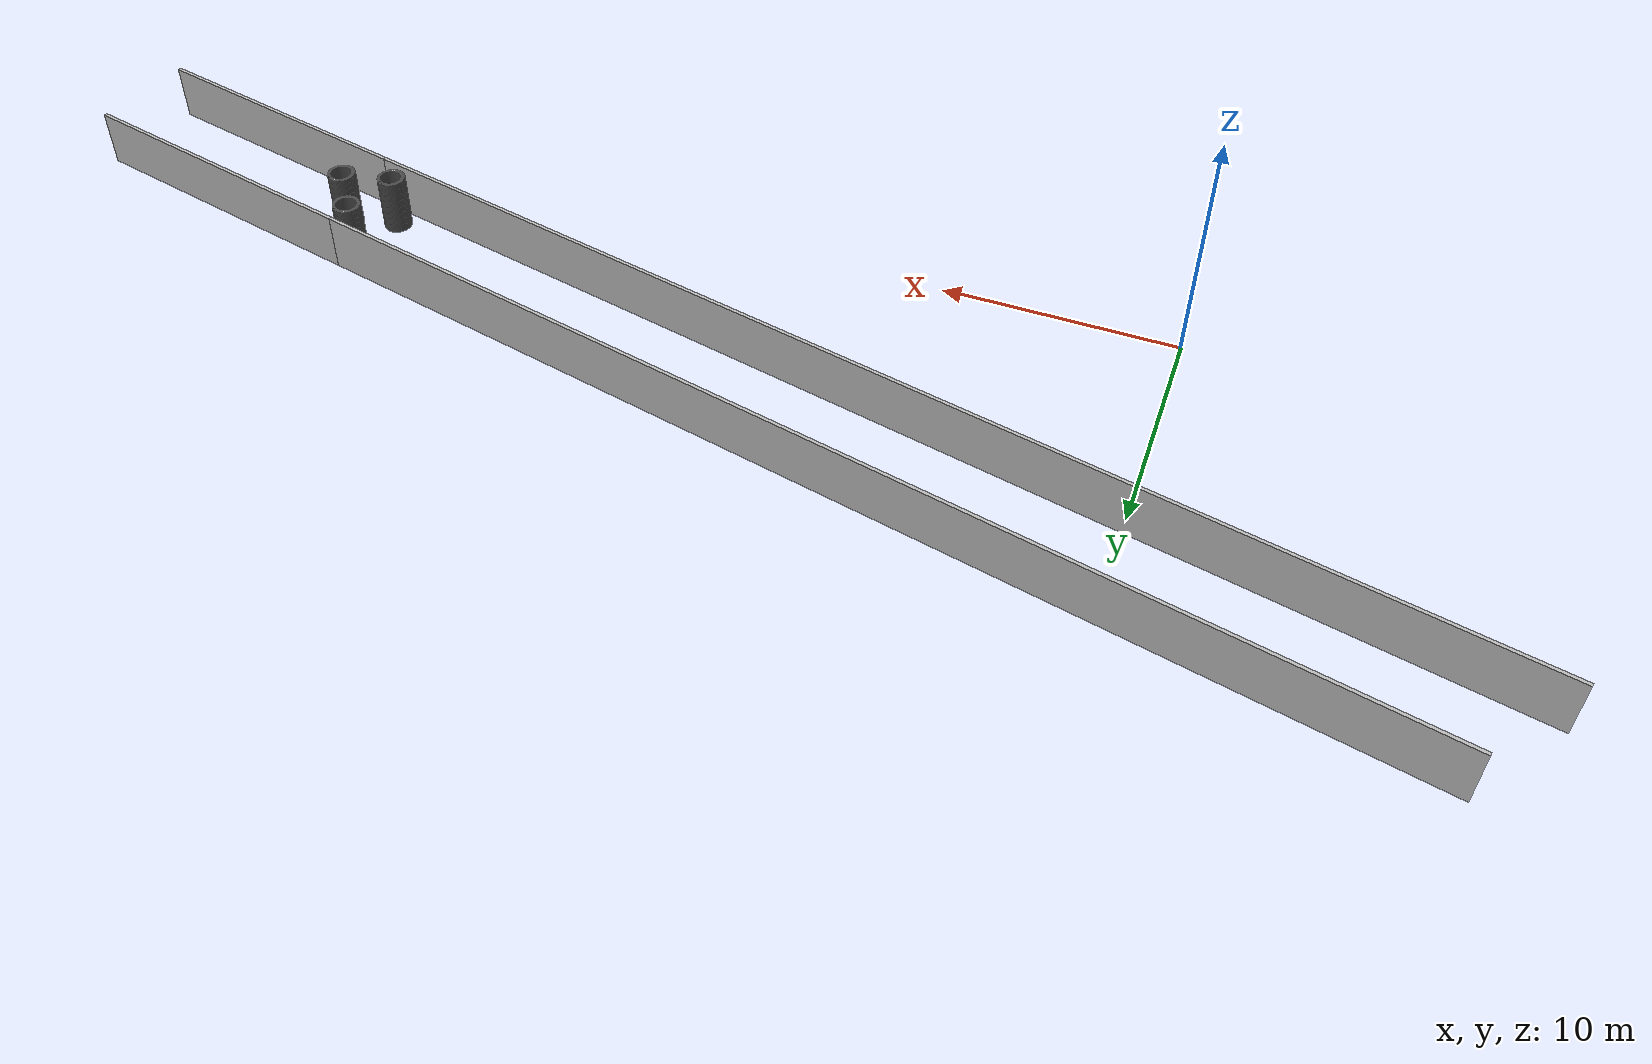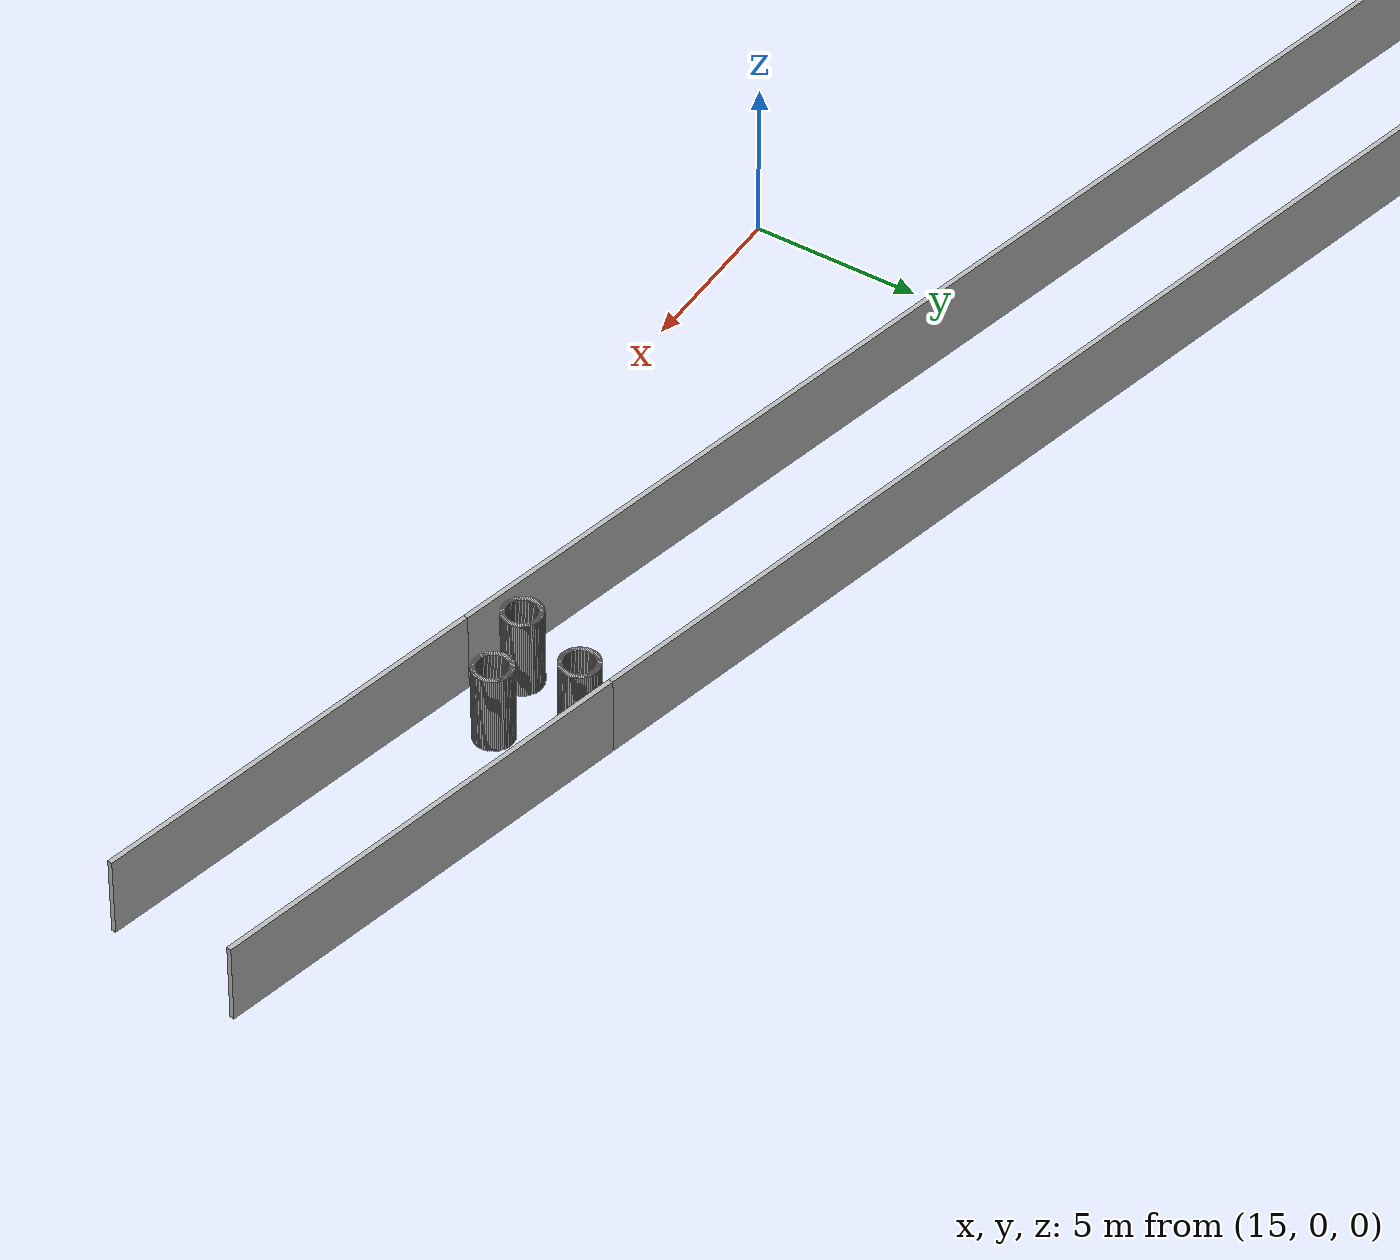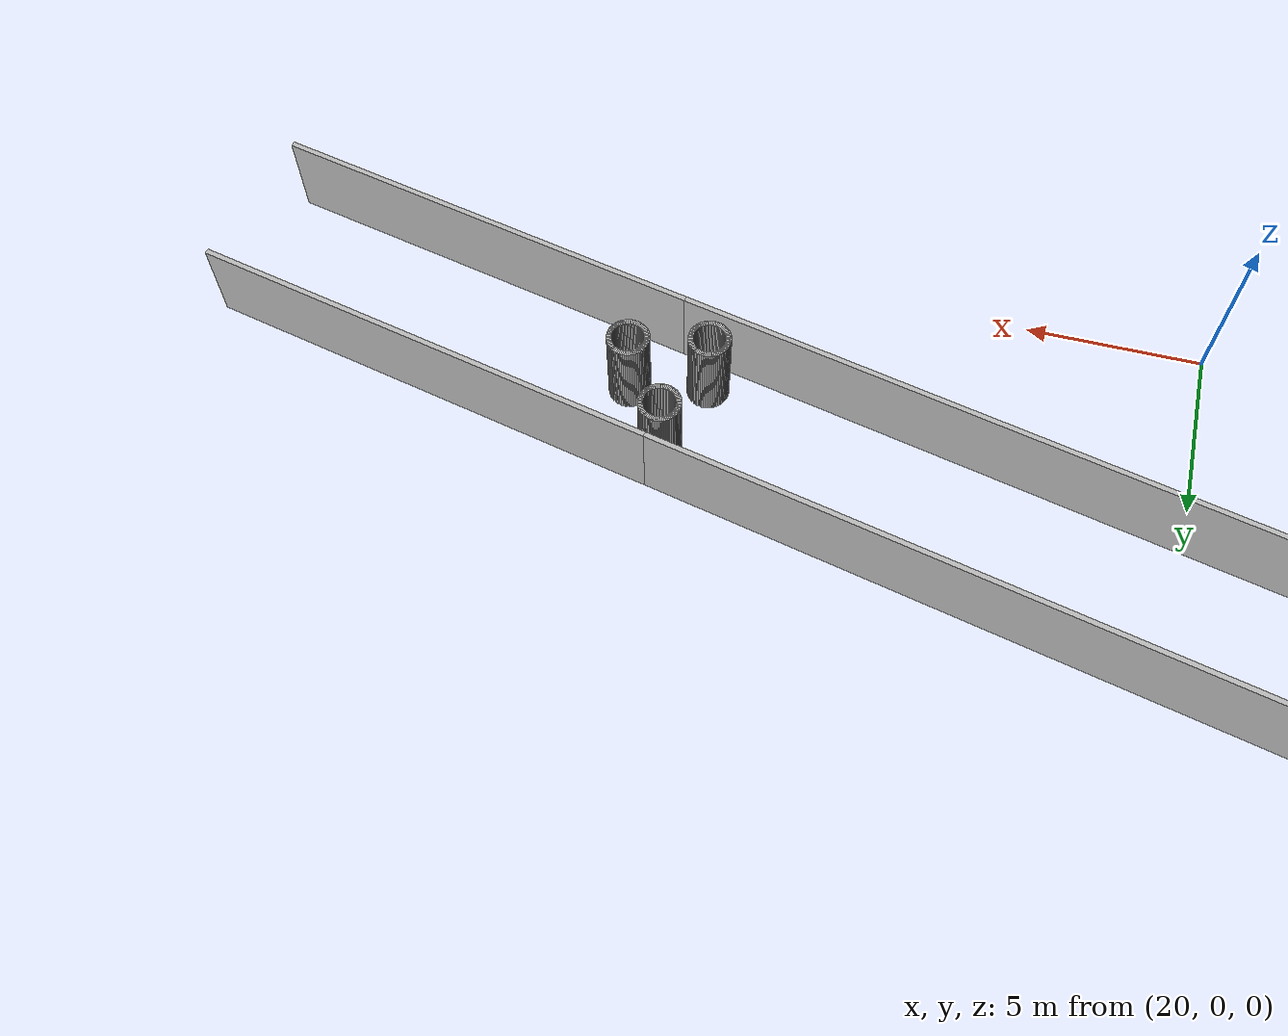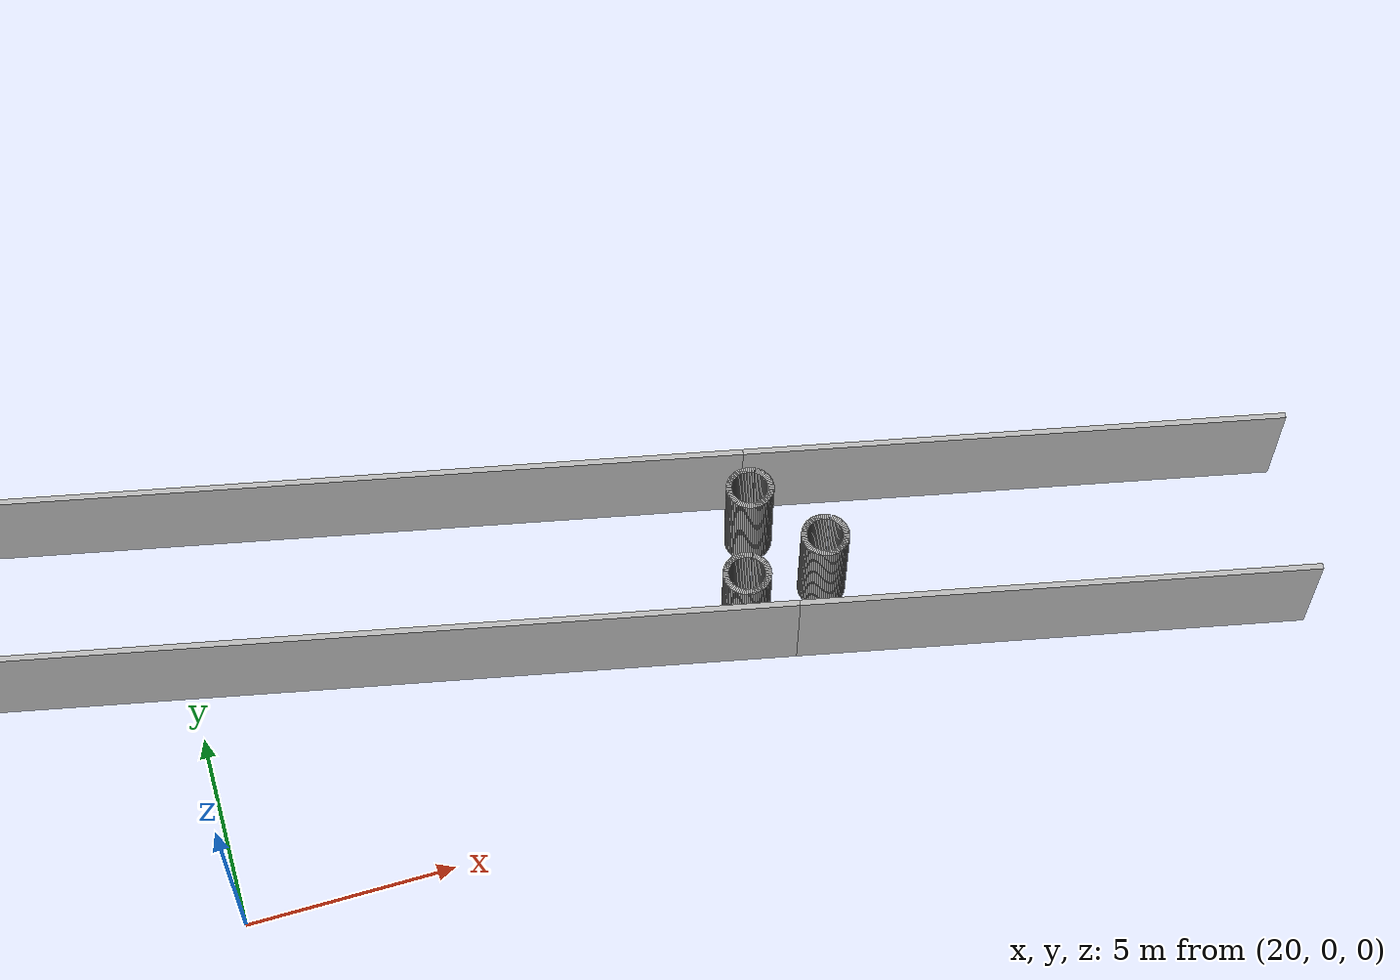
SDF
<?xml version="1.0" ?>
<sdf version="1.6">
  <model name="sps_2105">
    <pose frame="">0 0 0 0 -0 0</pose>
    <static>1</static>
    <self_collide>0</self_collide>
    <allow_auto_disable>0</allow_auto_disable>
    <link name="Wall360">
      <kinematic>0</kinematic>
      <gravity>1</gravity>
      <self_collide>0</self_collide>
      <collision name="collision">
        <geometry>
          <box>
            <size>12.6978 0.15 2.5</size>
          </box>
        </geometry>
        <pose frame="">0 0 0 0 -0 0</pose>
      </collision>
      <visual name="visual">
        <geometry>
          <box>
            <size>12.6978 0.15 2.5</size>
          </box>
        </geometry>
        <pose frame="">0 0 0 0 -0 0</pose>
        <cast_shadows>1</cast_shadows>
        <transparency>0.0</transparency>
      </visual>
      <pose frame="">40.6731 1.7684 1.25 0 -0 2.9273</pose>
    </link>
    <link name="Wall361">
      <kinematic>0</kinematic>
      <gravity>1</gravity>
      <self_collide>0</self_collide>
      <collision name="collision">
        <geometry>
          <box>
            <size>51.1704 0.15 2.5</size>
          </box>
        </geometry>
        <pose frame="">0 0 0 0 -0 0</pose>
      </collision>
      <visual name="visual">
        <geometry>
          <box>
            <size>51.1704 0.15 2.5</size>
          </box>
        </geometry>
        <pose frame="">0 0 0 0 -0 0</pose>
        <cast_shadows>1</cast_shadows>
        <transparency>0.0</transparency>
      </visual>
      <pose frame="">9.46944 8.55928 1.25 0 -0 2.9273</pose>
    </link>
    <link name="Wall540">
      <kinematic>0</kinematic>
      <gravity>1</gravity>
      <self_collide>0</self_collide>
      <collision name="collision">
        <geometry>
          <box>
            <size>13.6549 0.15 2.5</size>
          </box>
        </geometry>
        <pose frame="">0 0 0 0 -0 0</pose>
      </collision>
      <visual name="visual">
        <geometry>
          <box>
            <size>13.6549 0.15 2.5</size>
          </box>
        </geometry>
        <pose frame="">0 0 0 0 -0 0</pose>
        <cast_shadows>1</cast_shadows>
        <transparency>0.0</transparency>
      </visual>
      <pose frame="">41.1407 6.16955 1.25 0 -0 2.9273</pose>
    </link>
    <link name="Wall541">
      <kinematic>0</kinematic>
      <gravity>1</gravity>
      <self_collide>0</self_collide>
      <collision name="collision">
        <geometry>
          <box>
            <size>48.3021 0.15 2.5</size>
          </box>
        </geometry>
        <pose frame="">0 0 0 0 -0 0</pose>
      </collision>
      <visual name="visual">
        <geometry>
          <box>
            <size>48.3021 0.15 2.5</size>
          </box>
        </geometry>
        <pose frame="">0 0 0 0 -0 0</pose>
        <cast_shadows>1</cast_shadows>
        <transparency>0.0</transparency>
      </visual>
      <pose frame="">10.8708 12.7573 1.25 0 -0 2.9273</pose>
    </link>
    <link name="Wall907">
      <kinematic>0</kinematic>
      <gravity>1</gravity>
      <self_collide>0</self_collide>
      <collision name="collision">
        <geometry>
          <box>
            <size>0.0453637 0.15 2.5</size>
          </box>
        </geometry>
        <pose frame="">0 0 0 0 -0 0</pose>
      </collision>
      <visual name="visual">
        <geometry>
          <box>
            <size>0.0453637 0.15 2.5</size>
          </box>
        </geometry>
        <pose frame="">0 0 0 0 -0 0</pose>
        <cast_shadows>1</cast_shadows>
        <transparency>0.0</transparency>
      </visual>
      <pose frame="">35.9802 5.15571 1.25 0 0 -0.653727</pose>
    </link>
    <link name="Wall908">
      <kinematic>0</kinematic>
      <gravity>1</gravity>
      <self_collide>0</self_collide>
      <collision name="collision">
        <geometry>
          <box>
            <size>0.0453148 0.15 2.5</size>
          </box>
        </geometry>
        <pose frame="">0 0 0 0 -0 0</pose>
      </collision>
      <visual name="visual">
        <geometry>
          <box>
            <size>0.0453148 0.15 2.5</size>
          </box>
        </geometry>
        <pose frame="">0 0 0 0 -0 0</pose>
        <cast_shadows>1</cast_shadows>
        <transparency>0.0</transparency>
      </visual>
      <pose frame="">36.0149 5.1266 1.25 0 0 -0.742526</pose>
    </link>
    <link name="Wall909">
      <kinematic>0</kinematic>
      <gravity>1</gravity>
      <self_collide>0</self_collide>
      <collision name="collision">
        <geometry>
          <box>
            <size>0.0454498 0.15 2.5</size>
          </box>
        </geometry>
        <pose frame="">0 0 0 0 -0 0</pose>
      </collision>
      <visual name="visual">
        <geometry>
          <box>
            <size>0.0454498 0.15 2.5</size>
          </box>
        </geometry>
        <pose frame="">0 0 0 0 -0 0</pose>
        <cast_shadows>1</cast_shadows>
        <transparency>0.0</transparency>
      </visual>
      <pose frame="">36.047 5.0945 1.25 0 0 -0.830994</pose>
    </link>
    <link name="Wall910">
      <kinematic>0</kinematic>
      <gravity>1</gravity>
      <self_collide>0</self_collide>
      <collision name="collision">
        <geometry>
          <box>
            <size>0.0453637 0.15 2.5</size>
          </box>
        </geometry>
        <pose frame="">0 0 0 0 -0 0</pose>
      </collision>
      <visual name="visual">
        <geometry>
          <box>
            <size>0.0453637 0.15 2.5</size>
          </box>
        </geometry>
        <pose frame="">0 0 0 0 -0 0</pose>
        <cast_shadows>1</cast_shadows>
        <transparency>0.0</transparency>
      </visual>
      <pose frame="">36.0761 5.05971 1.25 0 0 -0.91707</pose>
    </link>
    <link name="Wall911">
      <kinematic>0</kinematic>
      <gravity>1</gravity>
      <self_collide>0</self_collide>
      <collision name="collision">
        <geometry>
          <box>
            <size>0.045342 0.15 2.5</size>
          </box>
        </geometry>
        <pose frame="">0 0 0 0 -0 0</pose>
      </collision>
      <visual name="visual">
        <geometry>
          <box>
            <size>0.045342 0.15 2.5</size>
          </box>
        </geometry>
        <pose frame="">0 0 0 0 -0 0</pose>
        <cast_shadows>1</cast_shadows>
        <transparency>0.0</transparency>
      </visual>
      <pose frame="">36.1021 5.0226 1.25 0 0 -1.00221</pose>
    </link>
    <link name="Wall912">
      <kinematic>0</kinematic>
      <gravity>1</gravity>
      <self_collide>0</self_collide>
      <collision name="collision">
        <geometry>
          <box>
            <size>0.0453724 0.15 2.5</size>
          </box>
        </geometry>
        <pose frame="">0 0 0 0 -0 0</pose>
      </collision>
      <visual name="visual">
        <geometry>
          <box>
            <size>0.0453724 0.15 2.5</size>
          </box>
        </geometry>
        <pose frame="">0 0 0 0 -0 0</pose>
        <cast_shadows>1</cast_shadows>
        <transparency>0.0</transparency>
      </visual>
      <pose frame="">36.1248 4.98338 1.25 0 0 -1.0897</pose>
    </link>
    <link name="Wall913">
      <kinematic>0</kinematic>
      <gravity>1</gravity>
      <self_collide>0</self_collide>
      <collision name="collision">
        <geometry>
          <box>
            <size>0.0454525 0.15 2.5</size>
          </box>
        </geometry>
        <pose frame="">0 0 0 0 -0 0</pose>
      </collision>
      <visual name="visual">
        <geometry>
          <box>
            <size>0.0454525 0.15 2.5</size>
          </box>
        </geometry>
        <pose frame="">0 0 0 0 -0 0</pose>
        <cast_shadows>1</cast_shadows>
        <transparency>0.0</transparency>
      </visual>
      <pose frame="">36.144 4.94227 1.25 0 0 -1.17807</pose>
    </link>
    <link name="Wall914">
      <kinematic>0</kinematic>
      <gravity>1</gravity>
      <self_collide>0</self_collide>
      <collision name="collision">
        <geometry>
          <box>
            <size>0.0453057 0.15 2.5</size>
          </box>
        </geometry>
        <pose frame="">0 0 0 0 -0 0</pose>
      </collision>
      <visual name="visual">
        <geometry>
          <box>
            <size>0.0453057 0.15 2.5</size>
          </box>
        </geometry>
        <pose frame="">0 0 0 0 -0 0</pose>
        <cast_shadows>1</cast_shadows>
        <transparency>0.0</transparency>
      </visual>
      <pose frame="">36.1595 4.89967 1.25 0 0 -1.26566</pose>
    </link>
    <link name="Wall915">
      <kinematic>0</kinematic>
      <gravity>1</gravity>
      <self_collide>0</self_collide>
      <collision name="collision">
        <geometry>
          <box>
            <size>0.0452557 0.15 2.5</size>
          </box>
        </geometry>
        <pose frame="">0 0 0 0 -0 0</pose>
      </collision>
      <visual name="visual">
        <geometry>
          <box>
            <size>0.0452557 0.15 2.5</size>
          </box>
        </geometry>
        <pose frame="">0 0 0 0 -0 0</pose>
        <cast_shadows>1</cast_shadows>
        <transparency>0.0</transparency>
      </visual>
      <pose frame="">36.1712 4.85597 1.25 0 0 -1.3533</pose>
    </link>
    <link name="Wall916">
      <kinematic>0</kinematic>
      <gravity>1</gravity>
      <self_collide>0</self_collide>
      <collision name="collision">
        <geometry>
          <box>
            <size>0.0453551 0.15 2.5</size>
          </box>
        </geometry>
        <pose frame="">0 0 0 0 -0 0</pose>
      </collision>
      <visual name="visual">
        <geometry>
          <box>
            <size>0.0453551 0.15 2.5</size>
          </box>
        </geometry>
        <pose frame="">0 0 0 0 -0 0</pose>
        <cast_shadows>1</cast_shadows>
        <transparency>0.0</transparency>
      </visual>
      <pose frame="">36.1789 4.81139 1.25 0 0 -1.4426</pose>
    </link>
    <link name="Wall917">
      <kinematic>0</kinematic>
      <gravity>1</gravity>
      <self_collide>0</self_collide>
      <collision name="collision">
        <geometry>
          <box>
            <size>0.0454548 0.15 2.5</size>
          </box>
        </geometry>
        <pose frame="">0 0 0 0 -0 0</pose>
      </collision>
      <visual name="visual">
        <geometry>
          <box>
            <size>0.0454548 0.15 2.5</size>
          </box>
        </geometry>
        <pose frame="">0 0 0 0 -0 0</pose>
        <cast_shadows>1</cast_shadows>
        <transparency>0.0</transparency>
      </visual>
      <pose frame="">36.1829 4.76619 1.25 0 0 -1.52647</pose>
    </link>
    <link name="Wall918">
      <kinematic>0</kinematic>
      <gravity>1</gravity>
      <self_collide>0</self_collide>
      <collision name="collision">
        <geometry>
          <box>
            <size>0.0454548 0.15 2.5</size>
          </box>
        </geometry>
        <pose frame="">0 0 0 0 -0 0</pose>
      </collision>
      <visual name="visual">
        <geometry>
          <box>
            <size>0.0454548 0.15 2.5</size>
          </box>
        </geometry>
        <pose frame="">0 0 0 0 -0 0</pose>
        <cast_shadows>1</cast_shadows>
        <transparency>0.0</transparency>
      </visual>
      <pose frame="">36.1829 4.72078 1.25 0 0 -1.61512</pose>
    </link>
    <link name="Wall919">
      <kinematic>0</kinematic>
      <gravity>1</gravity>
      <self_collide>0</self_collide>
      <collision name="collision">
        <geometry>
          <box>
            <size>0.0451735 0.15 2.5</size>
          </box>
        </geometry>
        <pose frame="">0 0 0 0 -0 0</pose>
      </collision>
      <visual name="visual">
        <geometry>
          <box>
            <size>0.0451735 0.15 2.5</size>
          </box>
        </geometry>
        <pose frame="">0 0 0 0 -0 0</pose>
        <cast_shadows>1</cast_shadows>
        <transparency>0.0</transparency>
      </visual>
      <pose frame="">36.1789 4.67567 1.25 0 0 -1.69951</pose>
    </link>
    <link name="Wall920">
      <kinematic>0</kinematic>
      <gravity>1</gravity>
      <self_collide>0</self_collide>
      <collision name="collision">
        <geometry>
          <box>
            <size>0.0454876 0.15 2.5</size>
          </box>
        </geometry>
        <pose frame="">0 0 0 0 -0 0</pose>
      </collision>
      <visual name="visual">
        <geometry>
          <box>
            <size>0.0454876 0.15 2.5</size>
          </box>
        </geometry>
        <pose frame="">0 0 0 0 -0 0</pose>
        <cast_shadows>1</cast_shadows>
        <transparency>0.0</transparency>
      </visual>
      <pose frame="">36.171 4.63109 1.25 0 0 -1.79267</pose>
    </link>
    <link name="Wall921">
      <kinematic>0</kinematic>
      <gravity>1</gravity>
      <self_collide>0</self_collide>
      <collision name="collision">
        <geometry>
          <box>
            <size>0.0453057 0.15 2.5</size>
          </box>
        </geometry>
        <pose frame="">0 0 0 0 -0 0</pose>
      </collision>
      <visual name="visual">
        <geometry>
          <box>
            <size>0.0453057 0.15 2.5</size>
          </box>
        </geometry>
        <pose frame="">0 0 0 0 -0 0</pose>
        <cast_shadows>1</cast_shadows>
        <transparency>0.0</transparency>
      </visual>
      <pose frame="">36.1592 4.58729 1.25 0 0 -1.87593</pose>
    </link>
    <link name="Wall922">
      <kinematic>0</kinematic>
      <gravity>1</gravity>
      <self_collide>0</self_collide>
      <collision name="collision">
        <geometry>
          <box>
            <size>0.0454525 0.15 2.5</size>
          </box>
        </geometry>
        <pose frame="">0 0 0 0 -0 0</pose>
      </collision>
      <visual name="visual">
        <geometry>
          <box>
            <size>0.0454525 0.15 2.5</size>
          </box>
        </geometry>
        <pose frame="">0 0 0 0 -0 0</pose>
        <cast_shadows>1</cast_shadows>
        <transparency>0.0</transparency>
      </visual>
      <pose frame="">36.1437 4.54469 1.25 0 0 -1.96352</pose>
    </link>
    <link name="Wall923">
      <kinematic>0</kinematic>
      <gravity>1</gravity>
      <self_collide>0</self_collide>
      <collision name="collision">
        <geometry>
          <box>
            <size>0.0453724 0.15 2.5</size>
          </box>
        </geometry>
        <pose frame="">0 0 0 0 -0 0</pose>
      </collision>
      <visual name="visual">
        <geometry>
          <box>
            <size>0.0453724 0.15 2.5</size>
          </box>
        </geometry>
        <pose frame="">0 0 0 0 -0 0</pose>
        <cast_shadows>1</cast_shadows>
        <transparency>0.0</transparency>
      </visual>
      <pose frame="">36.1245 4.50358 1.25 0 0 -2.05189</pose>
    </link>
    <link name="Wall924">
      <kinematic>0</kinematic>
      <gravity>1</gravity>
      <self_collide>0</self_collide>
      <collision name="collision">
        <geometry>
          <box>
            <size>0.0453092 0.15 2.5</size>
          </box>
        </geometry>
        <pose frame="">0 0 0 0 -0 0</pose>
      </collision>
      <visual name="visual">
        <geometry>
          <box>
            <size>0.0453092 0.15 2.5</size>
          </box>
        </geometry>
        <pose frame="">0 0 0 0 -0 0</pose>
        <cast_shadows>1</cast_shadows>
        <transparency>0.0</transparency>
      </visual>
      <pose frame="">36.1019 4.46437 1.25 0 0 -2.13825</pose>
    </link>
    <link name="Wall925">
      <kinematic>0</kinematic>
      <gravity>1</gravity>
      <self_collide>0</self_collide>
      <collision name="collision">
        <geometry>
          <box>
            <size>0.0453524 0.15 2.5</size>
          </box>
        </geometry>
        <pose frame="">0 0 0 0 -0 0</pose>
      </collision>
      <visual name="visual">
        <geometry>
          <box>
            <size>0.0453524 0.15 2.5</size>
          </box>
        </geometry>
        <pose frame="">0 0 0 0 -0 0</pose>
        <cast_shadows>1</cast_shadows>
        <transparency>0.0</transparency>
      </visual>
      <pose frame="">36.0759 4.42729 1.25 0 0 -2.22641</pose>
    </link>
    <link name="Wall926">
      <kinematic>0</kinematic>
      <gravity>1</gravity>
      <self_collide>0</self_collide>
      <collision name="collision">
        <geometry>
          <box>
            <size>0.0453186 0.15 2.5</size>
          </box>
        </geometry>
        <pose frame="">0 0 0 0 -0 0</pose>
      </collision>
      <visual name="visual">
        <geometry>
          <box>
            <size>0.0453186 0.15 2.5</size>
          </box>
        </geometry>
        <pose frame="">0 0 0 0 -0 0</pose>
        <cast_shadows>1</cast_shadows>
        <transparency>0.0</transparency>
      </visual>
      <pose frame="">36.0467 4.39259 1.25 0 0 -2.31142</pose>
    </link>
    <link name="Wall927">
      <kinematic>0</kinematic>
      <gravity>1</gravity>
      <self_collide>0</self_collide>
      <collision name="collision">
        <geometry>
          <box>
            <size>0.0453974 0.15 2.5</size>
          </box>
        </geometry>
        <pose frame="">0 0 0 0 -0 0</pose>
      </collision>
      <visual name="visual">
        <geometry>
          <box>
            <size>0.0453974 0.15 2.5</size>
          </box>
        </geometry>
        <pose frame="">0 0 0 0 -0 0</pose>
        <cast_shadows>1</cast_shadows>
        <transparency>0.0</transparency>
      </visual>
      <pose frame="">36.0148 4.36049 1.25 0 0 -2.39709</pose>
    </link>
    <link name="Wall928">
      <kinematic>0</kinematic>
      <gravity>1</gravity>
      <self_collide>0</self_collide>
      <collision name="collision">
        <geometry>
          <box>
            <size>0.0453637 0.15 2.5</size>
          </box>
        </geometry>
        <pose frame="">0 0 0 0 -0 0</pose>
      </collision>
      <visual name="visual">
        <geometry>
          <box>
            <size>0.0453637 0.15 2.5</size>
          </box>
        </geometry>
        <pose frame="">0 0 0 0 -0 0</pose>
        <cast_shadows>1</cast_shadows>
        <transparency>0.0</transparency>
      </visual>
      <pose frame="">35.9801 4.33131 1.25 0 0 -2.48787</pose>
    </link>
    <link name="Wall929">
      <kinematic>0</kinematic>
      <gravity>1</gravity>
      <self_collide>0</self_collide>
      <collision name="collision">
        <geometry>
          <box>
            <size>0.0452437 0.15 2.5</size>
          </box>
        </geometry>
        <pose frame="">0 0 0 0 -0 0</pose>
      </collision>
      <visual name="visual">
        <geometry>
          <box>
            <size>0.0452437 0.15 2.5</size>
          </box>
        </geometry>
        <pose frame="">0 0 0 0 -0 0</pose>
        <cast_shadows>1</cast_shadows>
        <transparency>0.0</transparency>
      </visual>
      <pose frame="">35.943 4.3054 1.25 0 0 -2.57642</pose>
    </link>
    <link name="Wall930">
      <kinematic>0</kinematic>
      <gravity>1</gravity>
      <self_collide>0</self_collide>
      <collision name="collision">
        <geometry>
          <box>
            <size>0.0455348 0.15 2.5</size>
          </box>
        </geometry>
        <pose frame="">0 0 0 0 -0 0</pose>
      </collision>
      <visual name="visual">
        <geometry>
          <box>
            <size>0.0455348 0.15 2.5</size>
          </box>
        </geometry>
        <pose frame="">0 0 0 0 -0 0</pose>
        <cast_shadows>1</cast_shadows>
        <transparency>0.0</transparency>
      </visual>
      <pose frame="">35.9036 4.28279 1.25 0 0 -2.66236</pose>
    </link>
    <link name="Wall931">
      <kinematic>0</kinematic>
      <gravity>1</gravity>
      <self_collide>0</self_collide>
      <collision name="collision">
        <geometry>
          <box>
            <size>0.0452834 0.15 2.5</size>
          </box>
        </geometry>
        <pose frame="">0 0 0 0 -0 0</pose>
      </collision>
      <visual name="visual">
        <geometry>
          <box>
            <size>0.0452834 0.15 2.5</size>
          </box>
        </geometry>
        <pose frame="">0 0 0 0 -0 0</pose>
        <cast_shadows>1</cast_shadows>
        <transparency>0.0</transparency>
      </visual>
      <pose frame="">35.8625 4.26359 1.25 0 0 -2.74732</pose>
    </link>
    <link name="Wall932">
      <kinematic>0</kinematic>
      <gravity>1</gravity>
      <self_collide>0</self_collide>
      <collision name="collision">
        <geometry>
          <box>
            <size>0.0454804 0.15 2.5</size>
          </box>
        </geometry>
        <pose frame="">0 0 0 0 -0 0</pose>
      </collision>
      <visual name="visual">
        <geometry>
          <box>
            <size>0.0454804 0.15 2.5</size>
          </box>
        </geometry>
        <pose frame="">0 0 0 0 -0 0</pose>
        <cast_shadows>1</cast_shadows>
        <transparency>0.0</transparency>
      </visual>
      <pose frame="">35.8199 4.24809 1.25 0 0 -2.83767</pose>
    </link>
    <link name="Wall933">
      <kinematic>0</kinematic>
      <gravity>1</gravity>
      <self_collide>0</self_collide>
      <collision name="collision">
        <geometry>
          <box>
            <size>0.0452557 0.15 2.5</size>
          </box>
        </geometry>
        <pose frame="">0 0 0 0 -0 0</pose>
      </collision>
      <visual name="visual">
        <geometry>
          <box>
            <size>0.0452557 0.15 2.5</size>
          </box>
        </geometry>
        <pose frame="">0 0 0 0 -0 0</pose>
        <cast_shadows>1</cast_shadows>
        <transparency>0.0</transparency>
      </visual>
      <pose frame="">35.7761 4.2364 1.25 0 0 -2.92409</pose>
    </link>
    <link name="Wall934">
      <kinematic>0</kinematic>
      <gravity>1</gravity>
      <self_collide>0</self_collide>
      <collision name="collision">
        <geometry>
          <box>
            <size>0.0453869 0.15 2.5</size>
          </box>
        </geometry>
        <pose frame="">0 0 0 0 -0 0</pose>
      </collision>
      <visual name="visual">
        <geometry>
          <box>
            <size>0.0453869 0.15 2.5</size>
          </box>
        </geometry>
        <pose frame="">0 0 0 0 -0 0</pose>
        <cast_shadows>1</cast_shadows>
        <transparency>0.0</transparency>
      </visual>
      <pose frame="">35.7316 4.2285 1.25 0 0 -3.00806</pose>
    </link>
    <link name="Wall935">
      <kinematic>0</kinematic>
      <gravity>1</gravity>
      <self_collide>0</self_collide>
      <collision name="collision">
        <geometry>
          <box>
            <size>0.0454446 0.15 2.5</size>
          </box>
        </geometry>
        <pose frame="">0 0 0 0 -0 0</pose>
      </collision>
      <visual name="visual">
        <geometry>
          <box>
            <size>0.0454446 0.15 2.5</size>
          </box>
        </geometry>
        <pose frame="">0 0 0 0 -0 0</pose>
        <cast_shadows>1</cast_shadows>
        <transparency>0.0</transparency>
      </visual>
      <pose frame="">35.6864 4.22459 1.25 0 0 -3.10263</pose>
    </link>
    <link name="Wall936">
      <kinematic>0</kinematic>
      <gravity>1</gravity>
      <self_collide>0</self_collide>
      <collision name="collision">
        <geometry>
          <box>
            <size>0.0452617 0.15 2.5</size>
          </box>
        </geometry>
        <pose frame="">0 0 0 0 -0 0</pose>
      </collision>
      <visual name="visual">
        <geometry>
          <box>
            <size>0.0452617 0.15 2.5</size>
          </box>
        </geometry>
        <pose frame="">0 0 0 0 -0 0</pose>
        <cast_shadows>1</cast_shadows>
        <transparency>0.0</transparency>
      </visual>
      <pose frame="">35.641 4.22459 1.25 0 -0 3.10248</pose>
    </link>
    <link name="Wall937">
      <kinematic>0</kinematic>
      <gravity>1</gravity>
      <self_collide>0</self_collide>
      <collision name="collision">
        <geometry>
          <box>
            <size>0.0453869 0.15 2.5</size>
          </box>
        </geometry>
        <pose frame="">0 0 0 0 -0 0</pose>
      </collision>
      <visual name="visual">
        <geometry>
          <box>
            <size>0.0453869 0.15 2.5</size>
          </box>
        </geometry>
        <pose frame="">0 0 0 0 -0 0</pose>
        <cast_shadows>1</cast_shadows>
        <transparency>0.0</transparency>
      </visual>
      <pose frame="">35.5959 4.2285 1.25 0 -0 3.00806</pose>
    </link>
    <link name="Wall938">
      <kinematic>0</kinematic>
      <gravity>1</gravity>
      <self_collide>0</self_collide>
      <collision name="collision">
        <geometry>
          <box>
            <size>0.0454742 0.15 2.5</size>
          </box>
        </geometry>
        <pose frame="">0 0 0 0 -0 0</pose>
      </collision>
      <visual name="visual">
        <geometry>
          <box>
            <size>0.0454742 0.15 2.5</size>
          </box>
        </geometry>
        <pose frame="">0 0 0 0 -0 0</pose>
        <cast_shadows>1</cast_shadows>
        <transparency>0.0</transparency>
      </visual>
      <pose frame="">35.5513 4.23649 1.25 0 -0 2.92103</pose>
    </link>
    <link name="Wall939">
      <kinematic>0</kinematic>
      <gravity>1</gravity>
      <self_collide>0</self_collide>
      <collision name="collision">
        <geometry>
          <box>
            <size>0.0453057 0.15 2.5</size>
          </box>
        </geometry>
        <pose frame="">0 0 0 0 -0 0</pose>
      </collision>
      <visual name="visual">
        <geometry>
          <box>
            <size>0.0453057 0.15 2.5</size>
          </box>
        </geometry>
        <pose frame="">0 0 0 0 -0 0</pose>
        <cast_shadows>1</cast_shadows>
        <transparency>0.0</transparency>
      </visual>
      <pose frame="">35.5075 4.24827 1.25 0 -0 2.83646</pose>
    </link>
    <link name="Wall940">
      <kinematic>0</kinematic>
      <gravity>1</gravity>
      <self_collide>0</self_collide>
      <collision name="collision">
        <geometry>
          <box>
            <size>0.0452834 0.15 2.5</size>
          </box>
        </geometry>
        <pose frame="">0 0 0 0 -0 0</pose>
      </collision>
      <visual name="visual">
        <geometry>
          <box>
            <size>0.0452834 0.15 2.5</size>
          </box>
        </geometry>
        <pose frame="">0 0 0 0 -0 0</pose>
        <cast_shadows>1</cast_shadows>
        <transparency>0.0</transparency>
      </visual>
      <pose frame="">35.465 4.26378 1.25 0 -0 2.74732</pose>
    </link>
    <link name="Wall941">
      <kinematic>0</kinematic>
      <gravity>1</gravity>
      <self_collide>0</self_collide>
      <collision name="collision">
        <geometry>
          <box>
            <size>0.045288 0.15 2.5</size>
          </box>
        </geometry>
        <pose frame="">0 0 0 0 -0 0</pose>
      </collision>
      <visual name="visual">
        <geometry>
          <box>
            <size>0.045288 0.15 2.5</size>
          </box>
        </geometry>
        <pose frame="">0 0 0 0 -0 0</pose>
        <cast_shadows>1</cast_shadows>
        <transparency>0.0</transparency>
      </visual>
      <pose frame="">35.4239 4.28288 1.25 0 -0 2.66408</pose>
    </link>
    <link name="Wall942">
      <kinematic>0</kinematic>
      <gravity>1</gravity>
      <self_collide>0</self_collide>
      <collision name="collision">
        <geometry>
          <box>
            <size>0.0454964 0.15 2.5</size>
          </box>
        </geometry>
        <pose frame="">0 0 0 0 -0 0</pose>
      </collision>
      <visual name="visual">
        <geometry>
          <box>
            <size>0.0454964 0.15 2.5</size>
          </box>
        </geometry>
        <pose frame="">0 0 0 0 -0 0</pose>
        <cast_shadows>1</cast_shadows>
        <transparency>0.0</transparency>
      </visual>
      <pose frame="">35.3846 4.3055 1.25 0 -0 2.57517</pose>
    </link>
    <link name="Wall943">
      <kinematic>0</kinematic>
      <gravity>1</gravity>
      <self_collide>0</self_collide>
      <collision name="collision">
        <geometry>
          <box>
            <size>0.0454753 0.15 2.5</size>
          </box>
        </geometry>
        <pose frame="">0 0 0 0 -0 0</pose>
      </collision>
      <visual name="visual">
        <geometry>
          <box>
            <size>0.0454753 0.15 2.5</size>
          </box>
        </geometry>
        <pose frame="">0 0 0 0 -0 0</pose>
        <cast_shadows>1</cast_shadows>
        <transparency>0.0</transparency>
      </visual>
      <pose frame="">35.3474 4.33159 1.25 0 -0 2.48467</pose>
    </link>
    <link name="Wall944">
      <kinematic>0</kinematic>
      <gravity>1</gravity>
      <self_collide>0</self_collide>
      <collision name="collision">
        <geometry>
          <box>
            <size>0.0453148 0.15 2.5</size>
          </box>
        </geometry>
        <pose frame="">0 0 0 0 -0 0</pose>
      </collision>
      <visual name="visual">
        <geometry>
          <box>
            <size>0.0453148 0.15 2.5</size>
          </box>
        </geometry>
        <pose frame="">0 0 0 0 -0 0</pose>
        <cast_shadows>1</cast_shadows>
        <transparency>0.0</transparency>
      </visual>
      <pose frame="">35.3127 4.36079 1.25 0 -0 2.39907</pose>
    </link>
    <link name="Wall945">
      <kinematic>0</kinematic>
      <gravity>1</gravity>
      <self_collide>0</self_collide>
      <collision name="collision">
        <geometry>
          <box>
            <size>0.0452735 0.15 2.5</size>
          </box>
        </geometry>
        <pose frame="">0 0 0 0 -0 0</pose>
      </collision>
      <visual name="visual">
        <geometry>
          <box>
            <size>0.0452735 0.15 2.5</size>
          </box>
        </geometry>
        <pose frame="">0 0 0 0 -0 0</pose>
        <cast_shadows>1</cast_shadows>
        <transparency>0.0</transparency>
      </visual>
      <pose frame="">35.2808 4.39281 1.25 0 -0 2.31233</pose>
    </link>
    <link name="Wall946">
      <kinematic>0</kinematic>
      <gravity>1</gravity>
      <self_collide>0</self_collide>
      <collision name="collision">
        <geometry>
          <box>
            <size>0.0453637 0.15 2.5</size>
          </box>
        </geometry>
        <pose frame="">0 0 0 0 -0 0</pose>
      </collision>
      <visual name="visual">
        <geometry>
          <box>
            <size>0.0453637 0.15 2.5</size>
          </box>
        </geometry>
        <pose frame="">0 0 0 0 -0 0</pose>
        <cast_shadows>1</cast_shadows>
        <transparency>0.0</transparency>
      </visual>
      <pose frame="">35.2517 4.4275 1.25 0 -0 2.22452</pose>
    </link>
    <link name="Wall947">
      <kinematic>0</kinematic>
      <gravity>1</gravity>
      <self_collide>0</self_collide>
      <collision name="collision">
        <geometry>
          <box>
            <size>0.045342 0.15 2.5</size>
          </box>
        </geometry>
        <pose frame="">0 0 0 0 -0 0</pose>
      </collision>
      <visual name="visual">
        <geometry>
          <box>
            <size>0.045342 0.15 2.5</size>
          </box>
        </geometry>
        <pose frame="">0 0 0 0 -0 0</pose>
        <cast_shadows>1</cast_shadows>
        <transparency>0.0</transparency>
      </visual>
      <pose frame="">35.2257 4.46461 1.25 0 -0 2.13938</pose>
    </link>
    <link name="Wall948">
      <kinematic>0</kinematic>
      <gravity>1</gravity>
      <self_collide>0</self_collide>
      <collision name="collision">
        <geometry>
          <box>
            <size>0.0453183 0.15 2.5</size>
          </box>
        </geometry>
        <pose frame="">0 0 0 0 -0 0</pose>
      </collision>
      <visual name="visual">
        <geometry>
          <box>
            <size>0.0453183 0.15 2.5</size>
          </box>
        </geometry>
        <pose frame="">0 0 0 0 -0 0</pose>
        <cast_shadows>1</cast_shadows>
        <transparency>0.0</transparency>
      </visual>
      <pose frame="">35.203 4.5038 1.25 0 -0 2.05251</pose>
    </link>
    <link name="Wall949">
      <kinematic>0</kinematic>
      <gravity>1</gravity>
      <self_collide>0</self_collide>
      <collision name="collision">
        <geometry>
          <box>
            <size>0.0453827 0.15 2.5</size>
          </box>
        </geometry>
        <pose frame="">0 0 0 0 -0 0</pose>
      </collision>
      <visual name="visual">
        <geometry>
          <box>
            <size>0.0453827 0.15 2.5</size>
          </box>
        </geometry>
        <pose frame="">0 0 0 0 -0 0</pose>
        <cast_shadows>1</cast_shadows>
        <transparency>0.0</transparency>
      </visual>
      <pose frame="">35.1839 4.54488 1.25 0 -0 1.95979</pose>
    </link>
    <link name="Wall950">
      <kinematic>0</kinematic>
      <gravity>1</gravity>
      <self_collide>0</self_collide>
      <collision name="collision">
        <geometry>
          <box>
            <size>0.0454804 0.15 2.5</size>
          </box>
        </geometry>
        <pose frame="">0 0 0 0 -0 0</pose>
      </collision>
      <visual name="visual">
        <geometry>
          <box>
            <size>0.0454804 0.15 2.5</size>
          </box>
        </geometry>
        <pose frame="">0 0 0 0 -0 0</pose>
        <cast_shadows>1</cast_shadows>
        <transparency>0.0</transparency>
      </visual>
      <pose frame="">35.1684 4.58757 1.25 0 -0 1.87472</pose>
    </link>
    <link name="Wall951">
      <kinematic>0</kinematic>
      <gravity>1</gravity>
      <self_collide>0</self_collide>
      <collision name="collision">
        <geometry>
          <box>
            <size>0.0453685 0.15 2.5</size>
          </box>
        </geometry>
        <pose frame="">0 0 0 0 -0 0</pose>
      </collision>
      <visual name="visual">
        <geometry>
          <box>
            <size>0.0453685 0.15 2.5</size>
          </box>
        </geometry>
        <pose frame="">0 0 0 0 -0 0</pose>
        <cast_shadows>1</cast_shadows>
        <transparency>0.0</transparency>
      </visual>
      <pose frame="">35.1566 4.63139 1.25 0 -0 1.79326</pose>
    </link>
    <link name="Wall952">
      <kinematic>0</kinematic>
      <gravity>1</gravity>
      <self_collide>0</self_collide>
      <collision name="collision">
        <geometry>
          <box>
            <size>0.0453551 0.15 2.5</size>
          </box>
        </geometry>
        <pose frame="">0 0 0 0 -0 0</pose>
      </collision>
      <visual name="visual">
        <geometry>
          <box>
            <size>0.0453551 0.15 2.5</size>
          </box>
        </geometry>
        <pose frame="">0 0 0 0 -0 0</pose>
        <cast_shadows>1</cast_shadows>
        <transparency>0.0</transparency>
      </visual>
      <pose frame="">35.1487 4.67601 1.25 0 -0 1.69899</pose>
    </link>
    <link name="Wall953">
      <kinematic>0</kinematic>
      <gravity>1</gravity>
      <self_collide>0</self_collide>
      <collision name="collision">
        <geometry>
          <box>
            <size>0.0452082 0.15 2.5</size>
          </box>
        </geometry>
        <pose frame="">0 0 0 0 -0 0</pose>
      </collision>
      <visual name="visual">
        <geometry>
          <box>
            <size>0.0452082 0.15 2.5</size>
          </box>
        </geometry>
        <pose frame="">0 0 0 0 -0 0</pose>
        <cast_shadows>1</cast_shadows>
        <transparency>0.0</transparency>
      </visual>
      <pose frame="">35.1449 4.72108 1.25 0 -0 1.61401</pose>
    </link>
    <link name="Wall954">
      <kinematic>0</kinematic>
      <gravity>1</gravity>
      <self_collide>0</self_collide>
      <collision name="collision">
        <geometry>
          <box>
            <size>0.0454521 0.15 2.5</size>
          </box>
        </geometry>
        <pose frame="">0 0 0 0 -0 0</pose>
      </collision>
      <visual name="visual">
        <geometry>
          <box>
            <size>0.0454521 0.15 2.5</size>
          </box>
        </geometry>
        <pose frame="">0 0 0 0 -0 0</pose>
        <cast_shadows>1</cast_shadows>
        <transparency>0.0</transparency>
      </visual>
      <pose frame="">35.1449 4.76637 1.25 0 -0 1.52781</pose>
    </link>
    <link name="Wall955">
      <kinematic>0</kinematic>
      <gravity>1</gravity>
      <self_collide>0</self_collide>
      <collision name="collision">
        <geometry>
          <box>
            <size>0.0454474 0.15 2.5</size>
          </box>
        </geometry>
        <pose frame="">0 0 0 0 -0 0</pose>
      </collision>
      <visual name="visual">
        <geometry>
          <box>
            <size>0.0454474 0.15 2.5</size>
          </box>
        </geometry>
        <pose frame="">0 0 0 0 -0 0</pose>
        <cast_shadows>1</cast_shadows>
        <transparency>0.0</transparency>
      </visual>
      <pose frame="">35.1489 4.8116 1.25 0 -0 1.43745</pose>
    </link>
    <link name="Wall956">
      <kinematic>0</kinematic>
      <gravity>1</gravity>
      <self_collide>0</self_collide>
      <collision name="collision">
        <geometry>
          <box>
            <size>0.0452557 0.15 2.5</size>
          </box>
        </geometry>
        <pose frame="">0 0 0 0 -0 0</pose>
      </collision>
      <visual name="visual">
        <geometry>
          <box>
            <size>0.0452557 0.15 2.5</size>
          </box>
        </geometry>
        <pose frame="">0 0 0 0 -0 0</pose>
        <cast_shadows>1</cast_shadows>
        <transparency>0.0</transparency>
      </visual>
      <pose frame="">35.1568 4.85622 1.25 0 -0 1.3533</pose>
    </link>
    <link name="Wall957">
      <kinematic>0</kinematic>
      <gravity>1</gravity>
      <self_collide>0</self_collide>
      <collision name="collision">
        <geometry>
          <box>
            <size>0.0454804 0.15 2.5</size>
          </box>
        </geometry>
        <pose frame="">0 0 0 0 -0 0</pose>
      </collision>
      <visual name="visual">
        <geometry>
          <box>
            <size>0.0454804 0.15 2.5</size>
          </box>
        </geometry>
        <pose frame="">0 0 0 0 -0 0</pose>
        <cast_shadows>1</cast_shadows>
        <transparency>0.0</transparency>
      </visual>
      <pose frame="">35.1684 4.90001 1.25 0 -0 1.26687</pose>
    </link>
    <link name="Wall958">
      <kinematic>0</kinematic>
      <gravity>1</gravity>
      <self_collide>0</self_collide>
      <collision name="collision">
        <geometry>
          <box>
            <size>0.0452834 0.15 2.5</size>
          </box>
        </geometry>
        <pose frame="">0 0 0 0 -0 0</pose>
      </collision>
      <visual name="visual">
        <geometry>
          <box>
            <size>0.0452834 0.15 2.5</size>
          </box>
        </geometry>
        <pose frame="">0 0 0 0 -0 0</pose>
        <cast_shadows>1</cast_shadows>
        <transparency>0.0</transparency>
      </visual>
      <pose frame="">35.184 4.94261 1.25 0 -0 1.17652</pose>
    </link>
    <link name="Wall959">
      <kinematic>0</kinematic>
      <gravity>1</gravity>
      <self_collide>0</self_collide>
      <collision name="collision">
        <geometry>
          <box>
            <size>0.0453183 0.15 2.5</size>
          </box>
        </geometry>
        <pose frame="">0 0 0 0 -0 0</pose>
      </collision>
      <visual name="visual">
        <geometry>
          <box>
            <size>0.0453183 0.15 2.5</size>
          </box>
        </geometry>
        <pose frame="">0 0 0 0 -0 0</pose>
        <cast_shadows>1</cast_shadows>
        <transparency>0.0</transparency>
      </visual>
      <pose frame="">35.2031 4.9836 1.25 0 -0 1.08908</pose>
    </link>
    <link name="Wall960">
      <kinematic>0</kinematic>
      <gravity>1</gravity>
      <self_collide>0</self_collide>
      <collision name="collision">
        <geometry>
          <box>
            <size>0.0454964 0.15 2.5</size>
          </box>
        </geometry>
        <pose frame="">0 0 0 0 -0 0</pose>
      </collision>
      <visual name="visual">
        <geometry>
          <box>
            <size>0.0454964 0.15 2.5</size>
          </box>
        </geometry>
        <pose frame="">0 0 0 0 -0 0</pose>
        <cast_shadows>1</cast_shadows>
        <transparency>0.0</transparency>
      </visual>
      <pose frame="">35.2259 5.02287 1.25 0 -0 1.00438</pose>
    </link>
    <link name="Wall961">
      <kinematic>0</kinematic>
      <gravity>1</gravity>
      <self_collide>0</self_collide>
      <collision name="collision">
        <geometry>
          <box>
            <size>0.0453637 0.15 2.5</size>
          </box>
        </geometry>
        <pose frame="">0 0 0 0 -0 0</pose>
      </collision>
      <visual name="visual">
        <geometry>
          <box>
            <size>0.0453637 0.15 2.5</size>
          </box>
        </geometry>
        <pose frame="">0 0 0 0 -0 0</pose>
        <cast_shadows>1</cast_shadows>
        <transparency>0.0</transparency>
      </visual>
      <pose frame="">35.2519 5.06007 1.25 0 -0 0.91707</pose>
    </link>
    <link name="Wall962">
      <kinematic>0</kinematic>
      <gravity>1</gravity>
      <self_collide>0</self_collide>
      <collision name="collision">
        <geometry>
          <box>
            <size>0.0452735 0.15 2.5</size>
          </box>
        </geometry>
        <pose frame="">0 0 0 0 -0 0</pose>
      </collision>
      <visual name="visual">
        <geometry>
          <box>
            <size>0.0452735 0.15 2.5</size>
          </box>
        </geometry>
        <pose frame="">0 0 0 0 -0 0</pose>
        <cast_shadows>1</cast_shadows>
        <transparency>0.0</transparency>
      </visual>
      <pose frame="">35.2809 5.09477 1.25 0 -0 0.829263</pose>
    </link>
    <link name="Wall963">
      <kinematic>0</kinematic>
      <gravity>1</gravity>
      <self_collide>0</self_collide>
      <collision name="collision">
        <geometry>
          <box>
            <size>0.0453598 0.15 2.5</size>
          </box>
        </geometry>
        <pose frame="">0 0 0 0 -0 0</pose>
      </collision>
      <visual name="visual">
        <geometry>
          <box>
            <size>0.0453598 0.15 2.5</size>
          </box>
        </geometry>
        <pose frame="">0 0 0 0 -0 0</pose>
        <cast_shadows>1</cast_shadows>
        <transparency>0.0</transparency>
      </visual>
      <pose frame="">35.3129 5.12678 1.25 0 -0 0.741617</pose>
    </link>
    <link name="Wall964">
      <kinematic>0</kinematic>
      <gravity>1</gravity>
      <self_collide>0</self_collide>
      <collision name="collision">
        <geometry>
          <box>
            <size>0.0453637 0.15 2.5</size>
          </box>
        </geometry>
        <pose frame="">0 0 0 0 -0 0</pose>
      </collision>
      <visual name="visual">
        <geometry>
          <box>
            <size>0.0453637 0.15 2.5</size>
          </box>
        </geometry>
        <pose frame="">0 0 0 0 -0 0</pose>
        <cast_shadows>1</cast_shadows>
        <transparency>0.0</transparency>
      </visual>
      <pose frame="">35.3477 5.1559 1.25 0 -0 0.653727</pose>
    </link>
    <link name="Wall965">
      <kinematic>0</kinematic>
      <gravity>1</gravity>
      <self_collide>0</self_collide>
      <collision name="collision">
        <geometry>
          <box>
            <size>0.0454964 0.15 2.5</size>
          </box>
        </geometry>
        <pose frame="">0 0 0 0 -0 0</pose>
      </collision>
      <visual name="visual">
        <geometry>
          <box>
            <size>0.0454964 0.15 2.5</size>
          </box>
        </geometry>
        <pose frame="">0 0 0 0 -0 0</pose>
        <cast_shadows>1</cast_shadows>
        <transparency>0.0</transparency>
      </visual>
      <pose frame="">35.3849 5.1819 1.25 0 -0 0.566421</pose>
    </link>
    <link name="Wall966">
      <kinematic>0</kinematic>
      <gravity>1</gravity>
      <self_collide>0</self_collide>
      <collision name="collision">
        <geometry>
          <box>
            <size>0.0452338 0.15 2.5</size>
          </box>
        </geometry>
        <pose frame="">0 0 0 0 -0 0</pose>
      </collision>
      <visual name="visual">
        <geometry>
          <box>
            <size>0.0452338 0.15 2.5</size>
          </box>
        </geometry>
        <pose frame="">0 0 0 0 -0 0</pose>
        <cast_shadows>1</cast_shadows>
        <transparency>0.0</transparency>
      </visual>
      <pose frame="">35.4242 5.20451 1.25 0 -0 0.478131</pose>
    </link>
    <link name="Wall967">
      <kinematic>0</kinematic>
      <gravity>1</gravity>
      <self_collide>0</self_collide>
      <collision name="collision">
        <geometry>
          <box>
            <size>0.0454525 0.15 2.5</size>
          </box>
        </geometry>
        <pose frame="">0 0 0 0 -0 0</pose>
      </collision>
      <visual name="visual">
        <geometry>
          <box>
            <size>0.0454525 0.15 2.5</size>
          </box>
        </geometry>
        <pose frame="">0 0 0 0 -0 0</pose>
        <cast_shadows>1</cast_shadows>
        <transparency>0.0</transparency>
      </visual>
      <pose frame="">35.4652 5.22362 1.25 0 -0 0.392725</pose>
    </link>
    <link name="Wall968">
      <kinematic>0</kinematic>
      <gravity>1</gravity>
      <self_collide>0</self_collide>
      <collision name="collision">
        <geometry>
          <box>
            <size>0.0452874 0.15 2.5</size>
          </box>
        </geometry>
        <pose frame="">0 0 0 0 -0 0</pose>
      </collision>
      <visual name="visual">
        <geometry>
          <box>
            <size>0.0452874 0.15 2.5</size>
          </box>
        </geometry>
        <pose frame="">0 0 0 0 -0 0</pose>
        <cast_shadows>1</cast_shadows>
        <transparency>0.0</transparency>
      </visual>
      <pose frame="">35.5078 5.23909 1.25 0 -0 0.30385</pose>
    </link>
    <link name="Wall969">
      <kinematic>0</kinematic>
      <gravity>1</gravity>
      <self_collide>0</self_collide>
      <collision name="collision">
        <geometry>
          <box>
            <size>0.0452689 0.15 2.5</size>
          </box>
        </geometry>
        <pose frame="">0 0 0 0 -0 0</pose>
      </collision>
      <visual name="visual">
        <geometry>
          <box>
            <size>0.0452689 0.15 2.5</size>
          </box>
        </geometry>
        <pose frame="">0 0 0 0 -0 0</pose>
        <cast_shadows>1</cast_shadows>
        <transparency>0.0</transparency>
      </visual>
      <pose frame="">35.5515 5.25078 1.25 0 -0 0.218815</pose>
    </link>
    <link name="Wall970">
      <kinematic>0</kinematic>
      <gravity>1</gravity>
      <self_collide>0</self_collide>
      <collision name="collision">
        <geometry>
          <box>
            <size>0.0454394 0.15 2.5</size>
          </box>
        </geometry>
        <pose frame="">0 0 0 0 -0 0</pose>
      </collision>
      <visual name="visual">
        <geometry>
          <box>
            <size>0.0454394 0.15 2.5</size>
          </box>
        </geometry>
        <pose frame="">0 0 0 0 -0 0</pose>
        <cast_shadows>1</cast_shadows>
        <transparency>0.0</transparency>
      </visual>
      <pose frame="">35.5962 5.25868 1.25 0 -0 0.132019</pose>
    </link>
    <link name="Wall971">
      <kinematic>0</kinematic>
      <gravity>1</gravity>
      <self_collide>0</self_collide>
      <collision name="collision">
        <geometry>
          <box>
            <size>0.0454548 0.15 2.5</size>
          </box>
        </geometry>
        <pose frame="">0 0 0 0 -0 0</pose>
      </collision>
      <visual name="visual">
        <geometry>
          <box>
            <size>0.0454548 0.15 2.5</size>
          </box>
        </geometry>
        <pose frame="">0 0 0 0 -0 0</pose>
        <cast_shadows>1</cast_shadows>
        <transparency>0.0</transparency>
      </visual>
      <pose frame="">35.6414 5.26268 1.25 0 -0 0.0443258</pose>
    </link>
    <link name="Wall972">
      <kinematic>0</kinematic>
      <gravity>1</gravity>
      <self_collide>0</self_collide>
      <collision name="collision">
        <geometry>
          <box>
            <size>0.0453938 0.15 2.5</size>
          </box>
        </geometry>
        <pose frame="">0 0 0 0 -0 0</pose>
      </collision>
      <visual name="visual">
        <geometry>
          <box>
            <size>0.0453938 0.15 2.5</size>
          </box>
        </geometry>
        <pose frame="">0 0 0 0 -0 0</pose>
        <cast_shadows>1</cast_shadows>
        <transparency>0.0</transparency>
      </visual>
      <pose frame="">35.6868 5.26268 1.25 0 0 -0.0443854</pose>
    </link>
    <link name="Wall973">
      <kinematic>0</kinematic>
      <gravity>1</gravity>
      <self_collide>0</self_collide>
      <collision name="collision">
        <geometry>
          <box>
            <size>0.0451973 0.15 2.5</size>
          </box>
        </geometry>
        <pose frame="">0 0 0 0 -0 0</pose>
      </collision>
      <visual name="visual">
        <geometry>
          <box>
            <size>0.0451973 0.15 2.5</size>
          </box>
        </geometry>
        <pose frame="">0 0 0 0 -0 0</pose>
        <cast_shadows>1</cast_shadows>
        <transparency>0.0</transparency>
      </visual>
      <pose frame="">35.7318 5.25868 1.25 0 0 -0.13273</pose>
    </link>
    <link name="Wall974">
      <kinematic>0</kinematic>
      <gravity>1</gravity>
      <self_collide>0</self_collide>
      <collision name="collision">
        <geometry>
          <box>
            <size>0.0455072 0.15 2.5</size>
          </box>
        </geometry>
        <pose frame="">0 0 0 0 -0 0</pose>
      </collision>
      <visual name="visual">
        <geometry>
          <box>
            <size>0.0455072 0.15 2.5</size>
          </box>
        </geometry>
        <pose frame="">0 0 0 0 -0 0</pose>
        <cast_shadows>1</cast_shadows>
        <transparency>0.0</transparency>
      </visual>
      <pose frame="">35.7765 5.25078 1.25 0 0 -0.217651</pose>
    </link>
    <link name="Wall975">
      <kinematic>0</kinematic>
      <gravity>1</gravity>
      <self_collide>0</self_collide>
      <collision name="collision">
        <geometry>
          <box>
            <size>0.0452874 0.15 2.5</size>
          </box>
        </geometry>
        <pose frame="">0 0 0 0 -0 0</pose>
      </collision>
      <visual name="visual">
        <geometry>
          <box>
            <size>0.0452874 0.15 2.5</size>
          </box>
        </geometry>
        <pose frame="">0 0 0 0 -0 0</pose>
        <cast_shadows>1</cast_shadows>
        <transparency>0.0</transparency>
      </visual>
      <pose frame="">35.8203 5.23909 1.25 0 0 -0.30385</pose>
    </link>
    <link name="Wall976">
      <kinematic>0</kinematic>
      <gravity>1</gravity>
      <self_collide>0</self_collide>
      <collision name="collision">
        <geometry>
          <box>
            <size>0.0454525 0.15 2.5</size>
          </box>
        </geometry>
        <pose frame="">0 0 0 0 -0 0</pose>
      </collision>
      <visual name="visual">
        <geometry>
          <box>
            <size>0.0454525 0.15 2.5</size>
          </box>
        </geometry>
        <pose frame="">0 0 0 0 -0 0</pose>
        <cast_shadows>1</cast_shadows>
        <transparency>0.0</transparency>
      </visual>
      <pose frame="">35.8629 5.22362 1.25 0 0 -0.392725</pose>
    </link>
    <link name="Wall977">
      <kinematic>0</kinematic>
      <gravity>1</gravity>
      <self_collide>0</self_collide>
      <collision name="collision">
        <geometry>
          <box>
            <size>0.0453183 0.15 2.5</size>
          </box>
        </geometry>
        <pose frame="">0 0 0 0 -0 0</pose>
      </collision>
      <visual name="visual">
        <geometry>
          <box>
            <size>0.0453183 0.15 2.5</size>
          </box>
        </geometry>
        <pose frame="">0 0 0 0 -0 0</pose>
        <cast_shadows>1</cast_shadows>
        <transparency>0.0</transparency>
      </visual>
      <pose frame="">35.904 5.20442 1.25 0 0 -0.481718</pose>
    </link>
    <link name="Wall1487">
      <kinematic>0</kinematic>
      <gravity>1</gravity>
      <self_collide>0</self_collide>
      <collision name="collision">
        <geometry>
          <box>
            <size>0.0455462 0.15 2.5</size>
          </box>
        </geometry>
        <pose frame="">0 0 0 0 -0 0</pose>
      </collision>
      <visual name="visual">
        <geometry>
          <box>
            <size>0.0455462 0.15 2.5</size>
          </box>
        </geometry>
        <pose frame="">0 0 0 0 -0 0</pose>
        <cast_shadows>1</cast_shadows>
        <transparency>0.0</transparency>
      </visual>
      <pose frame="">34.6379 6.98289 1.25 0 0 -0.652346</pose>
    </link>
    <link name="Wall1488">
      <kinematic>0</kinematic>
      <gravity>1</gravity>
      <self_collide>0</self_collide>
      <collision name="collision">
        <geometry>
          <box>
            <size>0.0453186 0.15 2.5</size>
          </box>
        </geometry>
        <pose frame="">0 0 0 0 -0 0</pose>
      </collision>
      <visual name="visual">
        <geometry>
          <box>
            <size>0.0453186 0.15 2.5</size>
          </box>
        </geometry>
        <pose frame="">0 0 0 0 -0 0</pose>
        <cast_shadows>1</cast_shadows>
        <transparency>0.0</transparency>
      </visual>
      <pose frame="">34.6728 6.95378 1.25 0 0 -0.740624</pose>
    </link>
    <link name="Wall1489">
      <kinematic>0</kinematic>
      <gravity>1</gravity>
      <self_collide>0</self_collide>
      <collision name="collision">
        <geometry>
          <box>
            <size>0.0454087 0.15 2.5</size>
          </box>
        </geometry>
        <pose frame="">0 0 0 0 -0 0</pose>
      </collision>
      <visual name="visual">
        <geometry>
          <box>
            <size>0.0454087 0.15 2.5</size>
          </box>
        </geometry>
        <pose frame="">0 0 0 0 -0 0</pose>
        <cast_shadows>1</cast_shadows>
        <transparency>0.0</transparency>
      </visual>
      <pose frame="">34.7048 6.92171 1.25 0 0 -0.831987</pose>
    </link>
    <link name="Wall1490">
      <kinematic>0</kinematic>
      <gravity>1</gravity>
      <self_collide>0</self_collide>
      <collision name="collision">
        <geometry>
          <box>
            <size>0.0453637 0.15 2.5</size>
          </box>
        </geometry>
        <pose frame="">0 0 0 0 -0 0</pose>
      </collision>
      <visual name="visual">
        <geometry>
          <box>
            <size>0.0453637 0.15 2.5</size>
          </box>
        </geometry>
        <pose frame="">0 0 0 0 -0 0</pose>
        <cast_shadows>1</cast_shadows>
        <transparency>0.0</transparency>
      </visual>
      <pose frame="">34.7338 6.88692 1.25 0 0 -0.91707</pose>
    </link>
    <link name="Wall1491">
      <kinematic>0</kinematic>
      <gravity>1</gravity>
      <self_collide>0</self_collide>
      <collision name="collision">
        <geometry>
          <box>
            <size>0.045342 0.15 2.5</size>
          </box>
        </geometry>
        <pose frame="">0 0 0 0 -0 0</pose>
      </collision>
      <visual name="visual">
        <geometry>
          <box>
            <size>0.045342 0.15 2.5</size>
          </box>
        </geometry>
        <pose frame="">0 0 0 0 -0 0</pose>
        <cast_shadows>1</cast_shadows>
        <transparency>0.0</transparency>
      </visual>
      <pose frame="">34.7598 6.84981 1.25 0 0 -1.00221</pose>
    </link>
    <link name="Wall1492">
      <kinematic>0</kinematic>
      <gravity>1</gravity>
      <self_collide>0</self_collide>
      <collision name="collision">
        <geometry>
          <box>
            <size>0.045288 0.15 2.5</size>
          </box>
        </geometry>
        <pose frame="">0 0 0 0 -0 0</pose>
      </collision>
      <visual name="visual">
        <geometry>
          <box>
            <size>0.045288 0.15 2.5</size>
          </box>
        </geometry>
        <pose frame="">0 0 0 0 -0 0</pose>
        <cast_shadows>1</cast_shadows>
        <transparency>0.0</transparency>
      </visual>
      <pose frame="">34.7825 6.81059 1.25 0 0 -1.09329</pose>
    </link>
    <link name="Wall1493">
      <kinematic>0</kinematic>
      <gravity>1</gravity>
      <self_collide>0</self_collide>
      <collision name="collision">
        <geometry>
          <box>
            <size>0.0454525 0.15 2.5</size>
          </box>
        </geometry>
        <pose frame="">0 0 0 0 -0 0</pose>
      </collision>
      <visual name="visual">
        <geometry>
          <box>
            <size>0.0454525 0.15 2.5</size>
          </box>
        </geometry>
        <pose frame="">0 0 0 0 -0 0</pose>
        <cast_shadows>1</cast_shadows>
        <transparency>0.0</transparency>
      </visual>
      <pose frame="">34.8016 6.76948 1.25 0 0 -1.17807</pose>
    </link>
    <link name="Wall1494">
      <kinematic>0</kinematic>
      <gravity>1</gravity>
      <self_collide>0</self_collide>
      <collision name="collision">
        <geometry>
          <box>
            <size>0.0453057 0.15 2.5</size>
          </box>
        </geometry>
        <pose frame="">0 0 0 0 -0 0</pose>
      </collision>
      <visual name="visual">
        <geometry>
          <box>
            <size>0.0453057 0.15 2.5</size>
          </box>
        </geometry>
        <pose frame="">0 0 0 0 -0 0</pose>
        <cast_shadows>1</cast_shadows>
        <transparency>0.0</transparency>
      </visual>
      <pose frame="">34.8171 6.72688 1.25 0 0 -1.26566</pose>
    </link>
    <link name="Wall1495">
      <kinematic>0</kinematic>
      <gravity>1</gravity>
      <self_collide>0</self_collide>
      <collision name="collision">
        <geometry>
          <box>
            <size>0.0454345 0.15 2.5</size>
          </box>
        </geometry>
        <pose frame="">0 0 0 0 -0 0</pose>
      </collision>
      <visual name="visual">
        <geometry>
          <box>
            <size>0.0454345 0.15 2.5</size>
          </box>
        </geometry>
        <pose frame="">0 0 0 0 -0 0</pose>
        <cast_shadows>1</cast_shadows>
        <transparency>0.0</transparency>
      </visual>
      <pose frame="">34.8288 6.68309 1.25 0 0 -1.35417</pose>
    </link>
    <link name="Wall1496">
      <kinematic>0</kinematic>
      <gravity>1</gravity>
      <self_collide>0</self_collide>
      <collision name="collision">
        <geometry>
          <box>
            <size>0.0453869 0.15 2.5</size>
          </box>
        </geometry>
        <pose frame="">0 0 0 0 -0 0</pose>
      </collision>
      <visual name="visual">
        <geometry>
          <box>
            <size>0.0453869 0.15 2.5</size>
          </box>
        </geometry>
        <pose frame="">0 0 0 0 -0 0</pose>
        <cast_shadows>1</cast_shadows>
        <transparency>0.0</transparency>
      </visual>
      <pose frame="">34.8367 6.63841 1.25 0 0 -1.43727</pose>
    </link>
    <link name="Wall1497">
      <kinematic>0</kinematic>
      <gravity>1</gravity>
      <self_collide>0</self_collide>
      <collision name="collision">
        <geometry>
          <box>
            <size>0.0452692 0.15 2.5</size>
          </box>
        </geometry>
        <pose frame="">0 0 0 0 -0 0</pose>
      </collision>
      <visual name="visual">
        <geometry>
          <box>
            <size>0.0452692 0.15 2.5</size>
          </box>
        </geometry>
        <pose frame="">0 0 0 0 -0 0</pose>
        <cast_shadows>1</cast_shadows>
        <transparency>0.0</transparency>
      </visual>
      <pose frame="">34.8407 6.59331 1.25 0 0 -1.52764</pose>
    </link>
    <link name="Wall1498">
      <kinematic>0</kinematic>
      <gravity>1</gravity>
      <self_collide>0</self_collide>
      <collision name="collision">
        <geometry>
          <box>
            <size>0.0454521 0.15 2.5</size>
          </box>
        </geometry>
        <pose frame="">0 0 0 0 -0 0</pose>
      </collision>
      <visual name="visual">
        <geometry>
          <box>
            <size>0.0454521 0.15 2.5</size>
          </box>
        </geometry>
        <pose frame="">0 0 0 0 -0 0</pose>
        <cast_shadows>1</cast_shadows>
        <transparency>0.0</transparency>
      </visual>
      <pose frame="">34.8407 6.54799 1.25 0 0 -1.61378</pose>
    </link>
    <link name="Wall1499">
      <kinematic>0</kinematic>
      <gravity>1</gravity>
      <self_collide>0</self_collide>
      <collision name="collision">
        <geometry>
          <box>
            <size>0.0453869 0.15 2.5</size>
          </box>
        </geometry>
        <pose frame="">0 0 0 0 -0 0</pose>
      </collision>
      <visual name="visual">
        <geometry>
          <box>
            <size>0.0453869 0.15 2.5</size>
          </box>
        </geometry>
        <pose frame="">0 0 0 0 -0 0</pose>
        <cast_shadows>1</cast_shadows>
        <transparency>0.0</transparency>
      </visual>
      <pose frame="">34.8367 6.50279 1.25 0 0 -1.70433</pose>
    </link>
    <link name="Wall1500">
      <kinematic>0</kinematic>
      <gravity>1</gravity>
      <self_collide>0</self_collide>
      <collision name="collision">
        <geometry>
          <box>
            <size>0.0452557 0.15 2.5</size>
          </box>
        </geometry>
        <pose frame="">0 0 0 0 -0 0</pose>
      </collision>
      <visual name="visual">
        <geometry>
          <box>
            <size>0.0452557 0.15 2.5</size>
          </box>
        </geometry>
        <pose frame="">0 0 0 0 -0 0</pose>
        <cast_shadows>1</cast_shadows>
        <transparency>0.0</transparency>
      </visual>
      <pose frame="">34.8288 6.45821 1.25 0 0 -1.78829</pose>
    </link>
    <link name="Wall1501">
      <kinematic>0</kinematic>
      <gravity>1</gravity>
      <self_collide>0</self_collide>
      <collision name="collision">
        <geometry>
          <box>
            <size>0.0453057 0.15 2.5</size>
          </box>
        </geometry>
        <pose frame="">0 0 0 0 -0 0</pose>
      </collision>
      <visual name="visual">
        <geometry>
          <box>
            <size>0.0453057 0.15 2.5</size>
          </box>
        </geometry>
        <pose frame="">0 0 0 0 -0 0</pose>
        <cast_shadows>1</cast_shadows>
        <transparency>0.0</transparency>
      </visual>
      <pose frame="">34.8171 6.4145 1.25 0 0 -1.87593</pose>
    </link>
    <link name="Wall1502">
      <kinematic>0</kinematic>
      <gravity>1</gravity>
      <self_collide>0</self_collide>
      <collision name="collision">
        <geometry>
          <box>
            <size>0.0454525 0.15 2.5</size>
          </box>
        </geometry>
        <pose frame="">0 0 0 0 -0 0</pose>
      </collision>
      <visual name="visual">
        <geometry>
          <box>
            <size>0.0454525 0.15 2.5</size>
          </box>
        </geometry>
        <pose frame="">0 0 0 0 -0 0</pose>
        <cast_shadows>1</cast_shadows>
        <transparency>0.0</transparency>
      </visual>
      <pose frame="">34.8016 6.3719 1.25 0 0 -1.96352</pose>
    </link>
    <link name="Wall1503">
      <kinematic>0</kinematic>
      <gravity>1</gravity>
      <self_collide>0</self_collide>
      <collision name="collision">
        <geometry>
          <box>
            <size>0.0453724 0.15 2.5</size>
          </box>
        </geometry>
        <pose frame="">0 0 0 0 -0 0</pose>
      </collision>
      <visual name="visual">
        <geometry>
          <box>
            <size>0.0453724 0.15 2.5</size>
          </box>
        </geometry>
        <pose frame="">0 0 0 0 -0 0</pose>
        <cast_shadows>1</cast_shadows>
        <transparency>0.0</transparency>
      </visual>
      <pose frame="">34.7824 6.33079 1.25 0 0 -2.05189</pose>
    </link>
    <link name="Wall1504">
      <kinematic>0</kinematic>
      <gravity>1</gravity>
      <self_collide>0</self_collide>
      <collision name="collision">
        <geometry>
          <box>
            <size>0.045342 0.15 2.5</size>
          </box>
        </geometry>
        <pose frame="">0 0 0 0 -0 0</pose>
      </collision>
      <visual name="visual">
        <geometry>
          <box>
            <size>0.045342 0.15 2.5</size>
          </box>
        </geometry>
        <pose frame="">0 0 0 0 -0 0</pose>
        <cast_shadows>1</cast_shadows>
        <transparency>0.0</transparency>
      </visual>
      <pose frame="">34.7597 6.29158 1.25 0 0 -2.13938</pose>
    </link>
    <link name="Wall1505">
      <kinematic>0</kinematic>
      <gravity>1</gravity>
      <self_collide>0</self_collide>
      <collision name="collision">
        <geometry>
          <box>
            <size>0.0453637 0.15 2.5</size>
          </box>
        </geometry>
        <pose frame="">0 0 0 0 -0 0</pose>
      </collision>
      <visual name="visual">
        <geometry>
          <box>
            <size>0.0453637 0.15 2.5</size>
          </box>
        </geometry>
        <pose frame="">0 0 0 0 -0 0</pose>
        <cast_shadows>1</cast_shadows>
        <transparency>0.0</transparency>
      </visual>
      <pose frame="">34.7337 6.25447 1.25 0 0 -2.22452</pose>
    </link>
    <link name="Wall1506">
      <kinematic>0</kinematic>
      <gravity>1</gravity>
      <self_collide>0</self_collide>
      <collision name="collision">
        <geometry>
          <box>
            <size>0.0453148 0.15 2.5</size>
          </box>
        </geometry>
        <pose frame="">0 0 0 0 -0 0</pose>
      </collision>
      <visual name="visual">
        <geometry>
          <box>
            <size>0.0453148 0.15 2.5</size>
          </box>
        </geometry>
        <pose frame="">0 0 0 0 -0 0</pose>
        <cast_shadows>1</cast_shadows>
        <transparency>0.0</transparency>
      </visual>
      <pose frame="">34.7046 6.21977 1.25 0 0 -2.31332</pose>
    </link>
    <link name="Wall1507">
      <kinematic>0</kinematic>
      <gravity>1</gravity>
      <self_collide>0</self_collide>
      <collision name="collision">
        <geometry>
          <box>
            <size>0.0455322 0.15 2.5</size>
          </box>
        </geometry>
        <pose frame="">0 0 0 0 -0 0</pose>
      </collision>
      <visual name="visual">
        <geometry>
          <box>
            <size>0.0455322 0.15 2.5</size>
          </box>
        </geometry>
        <pose frame="">0 0 0 0 -0 0</pose>
        <cast_shadows>1</cast_shadows>
        <transparency>0.0</transparency>
      </visual>
      <pose frame="">34.6724 6.1877 1.25 0 0 -2.39981</pose>
    </link>
    <link name="Wall1508">
      <kinematic>0</kinematic>
      <gravity>1</gravity>
      <self_collide>0</self_collide>
      <collision name="collision">
        <geometry>
          <box>
            <size>0.0454008 0.15 2.5</size>
          </box>
        </geometry>
        <pose frame="">0 0 0 0 -0 0</pose>
      </collision>
      <visual name="visual">
        <geometry>
          <box>
            <size>0.0454008 0.15 2.5</size>
          </box>
        </geometry>
        <pose frame="">0 0 0 0 -0 0</pose>
        <cast_shadows>1</cast_shadows>
        <transparency>0.0</transparency>
      </visual>
      <pose frame="">34.6377 6.15849 1.25 0 0 -2.4868</pose>
    </link>
    <link name="Wall1509">
      <kinematic>0</kinematic>
      <gravity>1</gravity>
      <self_collide>0</self_collide>
      <collision name="collision">
        <geometry>
          <box>
            <size>0.0453092 0.15 2.5</size>
          </box>
        </geometry>
        <pose frame="">0 0 0 0 -0 0</pose>
      </collision>
      <visual name="visual">
        <geometry>
          <box>
            <size>0.0453092 0.15 2.5</size>
          </box>
        </geometry>
        <pose frame="">0 0 0 0 -0 0</pose>
        <cast_shadows>1</cast_shadows>
        <transparency>0.0</transparency>
      </visual>
      <pose frame="">34.6005 6.13249 1.25 0 0 -2.57414</pose>
    </link>
    <link name="Wall1510">
      <kinematic>0</kinematic>
      <gravity>1</gravity>
      <self_collide>0</self_collide>
      <collision name="collision">
        <geometry>
          <box>
            <size>0.0452338 0.15 2.5</size>
          </box>
        </geometry>
        <pose frame="">0 0 0 0 -0 0</pose>
      </collision>
      <visual name="visual">
        <geometry>
          <box>
            <size>0.0452338 0.15 2.5</size>
          </box>
        </geometry>
        <pose frame="">0 0 0 0 -0 0</pose>
        <cast_shadows>1</cast_shadows>
        <transparency>0.0</transparency>
      </visual>
      <pose frame="">34.5614 6.10991 1.25 0 0 -2.66346</pose>
    </link>
    <link name="Wall1511">
      <kinematic>0</kinematic>
      <gravity>1</gravity>
      <self_collide>0</self_collide>
      <collision name="collision">
        <geometry>
          <box>
            <size>0.0455089 0.15 2.5</size>
          </box>
        </geometry>
        <pose frame="">0 0 0 0 -0 0</pose>
      </collision>
      <visual name="visual">
        <geometry>
          <box>
            <size>0.0455089 0.15 2.5</size>
          </box>
        </geometry>
        <pose frame="">0 0 0 0 -0 0</pose>
        <cast_shadows>1</cast_shadows>
        <transparency>0.0</transparency>
      </visual>
      <pose frame="">34.5203 6.0908 1.25 0 0 -2.74938</pose>
    </link>
    <link name="Wall1512">
      <kinematic>0</kinematic>
      <gravity>1</gravity>
      <self_collide>0</self_collide>
      <collision name="collision">
        <geometry>
          <box>
            <size>0.0452475 0.15 2.5</size>
          </box>
        </geometry>
        <pose frame="">0 0 0 0 -0 0</pose>
      </collision>
      <visual name="visual">
        <geometry>
          <box>
            <size>0.0452475 0.15 2.5</size>
          </box>
        </geometry>
        <pose frame="">0 0 0 0 -0 0</pose>
        <cast_shadows>1</cast_shadows>
        <transparency>0.0</transparency>
      </visual>
      <pose frame="">34.4777 6.0753 1.25 0 0 -2.83605</pose>
    </link>
    <link name="Wall1513">
      <kinematic>0</kinematic>
      <gravity>1</gravity>
      <self_collide>0</self_collide>
      <collision name="collision">
        <geometry>
          <box>
            <size>0.0455072 0.15 2.5</size>
          </box>
        </geometry>
        <pose frame="">0 0 0 0 -0 0</pose>
      </collision>
      <visual name="visual">
        <geometry>
          <box>
            <size>0.0455072 0.15 2.5</size>
          </box>
        </geometry>
        <pose frame="">0 0 0 0 -0 0</pose>
        <cast_shadows>1</cast_shadows>
        <transparency>0.0</transparency>
      </visual>
      <pose frame="">34.4339 6.06358 1.25 0 0 -2.92394</pose>
    </link>
    <link name="Wall1514">
      <kinematic>0</kinematic>
      <gravity>1</gravity>
      <self_collide>0</self_collide>
      <collision name="collision">
        <geometry>
          <box>
            <size>0.0451973 0.15 2.5</size>
          </box>
        </geometry>
        <pose frame="">0 0 0 0 -0 0</pose>
      </collision>
      <visual name="visual">
        <geometry>
          <box>
            <size>0.0451973 0.15 2.5</size>
          </box>
        </geometry>
        <pose frame="">0 0 0 0 -0 0</pose>
        <cast_shadows>1</cast_shadows>
        <transparency>0.0</transparency>
      </visual>
      <pose frame="">34.3892 6.05568 1.25 0 0 -3.00886</pose>
    </link>
    <link name="Wall1515">
      <kinematic>0</kinematic>
      <gravity>1</gravity>
      <self_collide>0</self_collide>
      <collision name="collision">
        <geometry>
          <box>
            <size>0.0454548 0.15 2.5</size>
          </box>
        </geometry>
        <pose frame="">0 0 0 0 -0 0</pose>
      </collision>
      <visual name="visual">
        <geometry>
          <box>
            <size>0.0454548 0.15 2.5</size>
          </box>
        </geometry>
        <pose frame="">0 0 0 0 -0 0</pose>
        <cast_shadows>1</cast_shadows>
        <transparency>0.0</transparency>
      </visual>
      <pose frame="">34.3441 6.05168 1.25 0 0 -3.09727</pose>
    </link>
    <link name="Wall1516">
      <kinematic>0</kinematic>
      <gravity>1</gravity>
      <self_collide>0</self_collide>
      <collision name="collision">
        <geometry>
          <box>
            <size>0.0454023 0.15 2.5</size>
          </box>
        </geometry>
        <pose frame="">0 0 0 0 -0 0</pose>
      </collision>
      <visual name="visual">
        <geometry>
          <box>
            <size>0.0454023 0.15 2.5</size>
          </box>
        </geometry>
        <pose frame="">0 0 0 0 -0 0</pose>
        <cast_shadows>1</cast_shadows>
        <transparency>0.0</transparency>
      </visual>
      <pose frame="">34.2988 6.05177 1.25 0 -0 3.09318</pose>
    </link>
    <link name="Wall1517">
      <kinematic>0</kinematic>
      <gravity>1</gravity>
      <self_collide>0</self_collide>
      <collision name="collision">
        <geometry>
          <box>
            <size>0.0454156 0.15 2.5</size>
          </box>
        </geometry>
        <pose frame="">0 0 0 0 -0 0</pose>
      </collision>
      <visual name="visual">
        <geometry>
          <box>
            <size>0.0454156 0.15 2.5</size>
          </box>
        </geometry>
        <pose frame="">0 0 0 0 -0 0</pose>
        <cast_shadows>1</cast_shadows>
        <transparency>0.0</transparency>
      </visual>
      <pose frame="">34.2536 6.05577 1.25 0 -0 3.01357</pose>
    </link>
    <link name="Wall1518">
      <kinematic>0</kinematic>
      <gravity>1</gravity>
      <self_collide>0</self_collide>
      <collision name="collision">
        <geometry>
          <box>
            <size>0.0452689 0.15 2.5</size>
          </box>
        </geometry>
        <pose frame="">0 0 0 0 -0 0</pose>
      </collision>
      <visual name="visual">
        <geometry>
          <box>
            <size>0.0452689 0.15 2.5</size>
          </box>
        </geometry>
        <pose frame="">0 0 0 0 -0 0</pose>
        <cast_shadows>1</cast_shadows>
        <transparency>0.0</transparency>
      </visual>
      <pose frame="">34.2089 6.06358 1.25 0 -0 2.92278</pose>
    </link>
    <link name="Wall1519">
      <kinematic>0</kinematic>
      <gravity>1</gravity>
      <self_collide>0</self_collide>
      <collision name="collision">
        <geometry>
          <box>
            <size>0.0453611 0.15 2.5</size>
          </box>
        </geometry>
        <pose frame="">0 0 0 0 -0 0</pose>
      </collision>
      <visual name="visual">
        <geometry>
          <box>
            <size>0.0453611 0.15 2.5</size>
          </box>
        </geometry>
        <pose frame="">0 0 0 0 -0 0</pose>
        <cast_shadows>1</cast_shadows>
        <transparency>0.0</transparency>
      </visual>
      <pose frame="">34.1652 6.07539 1.25 0 -0 2.83261</pose>
    </link>
    <link name="Wall1520">
      <kinematic>0</kinematic>
      <gravity>1</gravity>
      <self_collide>0</self_collide>
      <collision name="collision">
        <geometry>
          <box>
            <size>0.0453827 0.15 2.5</size>
          </box>
        </geometry>
        <pose frame="">0 0 0 0 -0 0</pose>
      </collision>
      <visual name="visual">
        <geometry>
          <box>
            <size>0.0453827 0.15 2.5</size>
          </box>
        </geometry>
        <pose frame="">0 0 0 0 -0 0</pose>
        <cast_shadows>1</cast_shadows>
        <transparency>0.0</transparency>
      </visual>
      <pose frame="">34.1226 6.0909 1.25 0 -0 2.75259</pose>
    </link>
    <link name="Wall1521">
      <kinematic>0</kinematic>
      <gravity>1</gravity>
      <self_collide>0</self_collide>
      <collision name="collision">
        <geometry>
          <box>
            <size>0.0453183 0.15 2.5</size>
          </box>
        </geometry>
        <pose frame="">0 0 0 0 -0 0</pose>
      </collision>
      <visual name="visual">
        <geometry>
          <box>
            <size>0.0453183 0.15 2.5</size>
          </box>
        </geometry>
        <pose frame="">0 0 0 0 -0 0</pose>
        <cast_shadows>1</cast_shadows>
        <transparency>0.0</transparency>
      </visual>
      <pose frame="">34.0816 6.11 1.25 0 -0 2.65987</pose>
    </link>
    <link name="Wall1522">
      <kinematic>0</kinematic>
      <gravity>1</gravity>
      <self_collide>0</self_collide>
      <collision name="collision">
        <geometry>
          <box>
            <size>0.045342 0.15 2.5</size>
          </box>
        </geometry>
        <pose frame="">0 0 0 0 -0 0</pose>
      </collision>
      <visual name="visual">
        <geometry>
          <box>
            <size>0.045342 0.15 2.5</size>
          </box>
        </geometry>
        <pose frame="">0 0 0 0 -0 0</pose>
        <cast_shadows>1</cast_shadows>
        <transparency>0.0</transparency>
      </visual>
      <pose frame="">34.0424 6.1327 1.25 0 -0 2.57301</pose>
    </link>
    <link name="Wall1523">
      <kinematic>0</kinematic>
      <gravity>1</gravity>
      <self_collide>0</self_collide>
      <collision name="collision">
        <geometry>
          <box>
            <size>0.0453637 0.15 2.5</size>
          </box>
        </geometry>
        <pose frame="">0 0 0 0 -0 0</pose>
      </collision>
      <visual name="visual">
        <geometry>
          <box>
            <size>0.0453637 0.15 2.5</size>
          </box>
        </geometry>
        <pose frame="">0 0 0 0 -0 0</pose>
        <cast_shadows>1</cast_shadows>
        <transparency>0.0</transparency>
      </visual>
      <pose frame="">34.0053 6.15871 1.25 0 -0 2.48787</pose>
    </link>
    <link name="Wall1524">
      <kinematic>0</kinematic>
      <gravity>1</gravity>
      <self_collide>0</self_collide>
      <collision name="collision">
        <geometry>
          <box>
            <size>0.0454539 0.15 2.5</size>
          </box>
        </geometry>
        <pose frame="">0 0 0 0 -0 0</pose>
      </collision>
      <visual name="visual">
        <geometry>
          <box>
            <size>0.0454539 0.15 2.5</size>
          </box>
        </geometry>
        <pose frame="">0 0 0 0 -0 0</pose>
        <cast_shadows>1</cast_shadows>
        <transparency>0.0</transparency>
      </visual>
      <pose frame="">33.9705 6.18779 1.25 0 -0 2.40369</pose>
    </link>
    <link name="Wall1525">
      <kinematic>0</kinematic>
      <gravity>1</gravity>
      <self_collide>0</self_collide>
      <collision name="collision">
        <geometry>
          <box>
            <size>0.0454539 0.15 2.5</size>
          </box>
        </geometry>
        <pose frame="">0 0 0 0 -0 0</pose>
      </collision>
      <visual name="visual">
        <geometry>
          <box>
            <size>0.0454539 0.15 2.5</size>
          </box>
        </geometry>
        <pose frame="">0 0 0 0 -0 0</pose>
        <cast_shadows>1</cast_shadows>
        <transparency>0.0</transparency>
      </visual>
      <pose frame="">33.9383 6.21989 1.25 0 -0 2.3087</pose>
    </link>
    <link name="Wall1526">
      <kinematic>0</kinematic>
      <gravity>1</gravity>
      <self_collide>0</self_collide>
      <collision name="collision">
        <geometry>
          <box>
            <size>0.0453637 0.15 2.5</size>
          </box>
        </geometry>
        <pose frame="">0 0 0 0 -0 0</pose>
      </collision>
      <visual name="visual">
        <geometry>
          <box>
            <size>0.0453637 0.15 2.5</size>
          </box>
        </geometry>
        <pose frame="">0 0 0 0 -0 0</pose>
        <cast_shadows>1</cast_shadows>
        <transparency>0.0</transparency>
      </visual>
      <pose frame="">33.9093 6.25471 1.25 0 -0 2.22452</pose>
    </link>
    <link name="Wall1527">
      <kinematic>0</kinematic>
      <gravity>1</gravity>
      <self_collide>0</self_collide>
      <collision name="collision">
        <geometry>
          <box>
            <size>0.0451922 0.15 2.5</size>
          </box>
        </geometry>
        <pose frame="">0 0 0 0 -0 0</pose>
      </collision>
      <visual name="visual">
        <geometry>
          <box>
            <size>0.0451922 0.15 2.5</size>
          </box>
        </geometry>
        <pose frame="">0 0 0 0 -0 0</pose>
        <cast_shadows>1</cast_shadows>
        <transparency>0.0</transparency>
      </visual>
      <pose frame="">33.8834 6.29179 1.25 0 -0 2.1367</pose>
    </link>
    <link name="Wall1528">
      <kinematic>0</kinematic>
      <gravity>1</gravity>
      <self_collide>0</self_collide>
      <collision name="collision">
        <geometry>
          <box>
            <size>0.0453724 0.15 2.5</size>
          </box>
        </geometry>
        <pose frame="">0 0 0 0 -0 0</pose>
      </collision>
      <visual name="visual">
        <geometry>
          <box>
            <size>0.0453724 0.15 2.5</size>
          </box>
        </geometry>
        <pose frame="">0 0 0 0 -0 0</pose>
        <cast_shadows>1</cast_shadows>
        <transparency>0.0</transparency>
      </visual>
      <pose frame="">33.8607 6.33098 1.25 0 -0 2.05189</pose>
    </link>
    <link name="Wall1529">
      <kinematic>0</kinematic>
      <gravity>1</gravity>
      <self_collide>0</self_collide>
      <collision name="collision">
        <geometry>
          <box>
            <size>0.0454525 0.15 2.5</size>
          </box>
        </geometry>
        <pose frame="">0 0 0 0 -0 0</pose>
      </collision>
      <visual name="visual">
        <geometry>
          <box>
            <size>0.0454525 0.15 2.5</size>
          </box>
        </geometry>
        <pose frame="">0 0 0 0 -0 0</pose>
        <cast_shadows>1</cast_shadows>
        <transparency>0.0</transparency>
      </visual>
      <pose frame="">33.8415 6.37208 1.25 0 -0 1.96352</pose>
    </link>
    <link name="Wall1530">
      <kinematic>0</kinematic>
      <gravity>1</gravity>
      <self_collide>0</self_collide>
      <collision name="collision">
        <geometry>
          <box>
            <size>0.0453057 0.15 2.5</size>
          </box>
        </geometry>
        <pose frame="">0 0 0 0 -0 0</pose>
      </collision>
      <visual name="visual">
        <geometry>
          <box>
            <size>0.0453057 0.15 2.5</size>
          </box>
        </geometry>
        <pose frame="">0 0 0 0 -0 0</pose>
        <cast_shadows>1</cast_shadows>
        <transparency>0.0</transparency>
      </visual>
      <pose frame="">33.826 6.41469 1.25 0 -0 1.87593</pose>
    </link>
    <link name="Wall1531">
      <kinematic>0</kinematic>
      <gravity>1</gravity>
      <self_collide>0</self_collide>
      <collision name="collision">
        <geometry>
          <box>
            <size>0.0454345 0.15 2.5</size>
          </box>
        </geometry>
        <pose frame="">0 0 0 0 -0 0</pose>
      </collision>
      <visual name="visual">
        <geometry>
          <box>
            <size>0.0454345 0.15 2.5</size>
          </box>
        </geometry>
        <pose frame="">0 0 0 0 -0 0</pose>
        <cast_shadows>1</cast_shadows>
        <transparency>0.0</transparency>
      </visual>
      <pose frame="">33.8144 6.45848 1.25 0 -0 1.78743</pose>
    </link>
    <link name="Wall1532">
      <kinematic>0</kinematic>
      <gravity>1</gravity>
      <self_collide>0</self_collide>
      <collision name="collision">
        <geometry>
          <box>
            <size>0.0454474 0.15 2.5</size>
          </box>
        </geometry>
        <pose frame="">0 0 0 0 -0 0</pose>
      </collision>
      <visual name="visual">
        <geometry>
          <box>
            <size>0.0454474 0.15 2.5</size>
          </box>
        </geometry>
        <pose frame="">0 0 0 0 -0 0</pose>
        <cast_shadows>1</cast_shadows>
        <transparency>0.0</transparency>
      </visual>
      <pose frame="">33.8064 6.50319 1.25 0 -0 1.70415</pose>
    </link>
    <link name="Wall1533">
      <kinematic>0</kinematic>
      <gravity>1</gravity>
      <self_collide>0</self_collide>
      <collision name="collision">
        <geometry>
          <box>
            <size>0.0452007 0.15 2.5</size>
          </box>
        </geometry>
        <pose frame="">0 0 0 0 -0 0</pose>
      </collision>
      <visual name="visual">
        <geometry>
          <box>
            <size>0.0452007 0.15 2.5</size>
          </box>
        </geometry>
        <pose frame="">0 0 0 0 -0 0</pose>
        <cast_shadows>1</cast_shadows>
        <transparency>0.0</transparency>
      </visual>
      <pose frame="">33.8025 6.54829 1.25 0 -0 1.60997</pose>
    </link>
    <link name="Wall1534">
      <kinematic>0</kinematic>
      <gravity>1</gravity>
      <self_collide>0</self_collide>
      <collision name="collision">
        <geometry>
          <box>
            <size>0.0454446 0.15 2.5</size>
          </box>
        </geometry>
        <pose frame="">0 0 0 0 -0 0</pose>
      </collision>
      <visual name="visual">
        <geometry>
          <box>
            <size>0.0454446 0.15 2.5</size>
          </box>
        </geometry>
        <pose frame="">0 0 0 0 -0 0</pose>
        <cast_shadows>1</cast_shadows>
        <transparency>0.0</transparency>
      </visual>
      <pose frame="">33.8025 6.59358 1.25 0 -0 1.53184</pose>
    </link>
    <link name="Wall1535">
      <kinematic>0</kinematic>
      <gravity>1</gravity>
      <self_collide>0</self_collide>
      <collision name="collision">
        <geometry>
          <box>
            <size>0.0453869 0.15 2.5</size>
          </box>
        </geometry>
        <pose frame="">0 0 0 0 -0 0</pose>
      </collision>
      <visual name="visual">
        <geometry>
          <box>
            <size>0.0453869 0.15 2.5</size>
          </box>
        </geometry>
        <pose frame="">0 0 0 0 -0 0</pose>
        <cast_shadows>1</cast_shadows>
        <transparency>0.0</transparency>
      </visual>
      <pose frame="">33.8064 6.63878 1.25 0 -0 1.43727</pose>
    </link>
    <link name="Wall1536">
      <kinematic>0</kinematic>
      <gravity>1</gravity>
      <self_collide>0</self_collide>
      <collision name="collision">
        <geometry>
          <box>
            <size>0.0453153 0.15 2.5</size>
          </box>
        </geometry>
        <pose frame="">0 0 0 0 -0 0</pose>
      </collision>
      <visual name="visual">
        <geometry>
          <box>
            <size>0.0453153 0.15 2.5</size>
          </box>
        </geometry>
        <pose frame="">0 0 0 0 -0 0</pose>
        <cast_shadows>1</cast_shadows>
        <transparency>0.0</transparency>
      </visual>
      <pose frame="">33.8144 6.68339 1.25 0 -0 1.35359</pose>
    </link>
    <link name="Wall1537">
      <kinematic>0</kinematic>
      <gravity>1</gravity>
      <self_collide>0</self_collide>
      <collision name="collision">
        <geometry>
          <box>
            <size>0.0453029 0.15 2.5</size>
          </box>
        </geometry>
        <pose frame="">0 0 0 0 -0 0</pose>
      </collision>
      <visual name="visual">
        <geometry>
          <box>
            <size>0.0453029 0.15 2.5</size>
          </box>
        </geometry>
        <pose frame="">0 0 0 0 -0 0</pose>
        <cast_shadows>1</cast_shadows>
        <transparency>0.0</transparency>
      </visual>
      <pose frame="">33.8261 6.7271 1.25 0 -0 1.2614</pose>
    </link>
    <link name="Wall1538">
      <kinematic>0</kinematic>
      <gravity>1</gravity>
      <self_collide>0</self_collide>
      <collision name="collision">
        <geometry>
          <box>
            <size>0.0453827 0.15 2.5</size>
          </box>
        </geometry>
        <pose frame="">0 0 0 0 -0 0</pose>
      </collision>
      <visual name="visual">
        <geometry>
          <box>
            <size>0.0453827 0.15 2.5</size>
          </box>
        </geometry>
        <pose frame="">0 0 0 0 -0 0</pose>
        <cast_shadows>1</cast_shadows>
        <transparency>0.0</transparency>
      </visual>
      <pose frame="">33.8416 6.76967 1.25 0 -0 1.1818</pose>
    </link>
    <link name="Wall1539">
      <kinematic>0</kinematic>
      <gravity>1</gravity>
      <self_collide>0</self_collide>
      <collision name="collision">
        <geometry>
          <box>
            <size>0.0453724 0.15 2.5</size>
          </box>
        </geometry>
        <pose frame="">0 0 0 0 -0 0</pose>
      </collision>
      <visual name="visual">
        <geometry>
          <box>
            <size>0.0453724 0.15 2.5</size>
          </box>
        </geometry>
        <pose frame="">0 0 0 0 -0 0</pose>
        <cast_shadows>1</cast_shadows>
        <transparency>0.0</transparency>
      </visual>
      <pose frame="">33.8607 6.81077 1.25 0 -0 1.0897</pose>
    </link>
    <link name="Wall1540">
      <kinematic>0</kinematic>
      <gravity>1</gravity>
      <self_collide>0</self_collide>
      <collision name="collision">
        <geometry>
          <box>
            <size>0.0454964 0.15 2.5</size>
          </box>
        </geometry>
        <pose frame="">0 0 0 0 -0 0</pose>
      </collision>
      <visual name="visual">
        <geometry>
          <box>
            <size>0.0454964 0.15 2.5</size>
          </box>
        </geometry>
        <pose frame="">0 0 0 0 -0 0</pose>
        <cast_shadows>1</cast_shadows>
        <transparency>0.0</transparency>
      </visual>
      <pose frame="">33.8834 6.85008 1.25 0 -0 1.00438</pose>
    </link>
    <link name="Wall1541">
      <kinematic>0</kinematic>
      <gravity>1</gravity>
      <self_collide>0</self_collide>
      <collision name="collision">
        <geometry>
          <box>
            <size>0.0452185 0.15 2.5</size>
          </box>
        </geometry>
        <pose frame="">0 0 0 0 -0 0</pose>
      </collision>
      <visual name="visual">
        <geometry>
          <box>
            <size>0.0452185 0.15 2.5</size>
          </box>
        </geometry>
        <pose frame="">0 0 0 0 -0 0</pose>
        <cast_shadows>1</cast_shadows>
        <transparency>0.0</transparency>
      </visual>
      <pose frame="">33.9094 6.88719 1.25 0 -0 0.914607</pose>
    </link>
    <link name="Wall1542">
      <kinematic>0</kinematic>
      <gravity>1</gravity>
      <self_collide>0</self_collide>
      <collision name="collision">
        <geometry>
          <box>
            <size>0.0455735 0.15 2.5</size>
          </box>
        </geometry>
        <pose frame="">0 0 0 0 -0 0</pose>
      </collision>
      <visual name="visual">
        <geometry>
          <box>
            <size>0.0455735 0.15 2.5</size>
          </box>
        </geometry>
        <pose frame="">0 0 0 0 -0 0</pose>
        <cast_shadows>1</cast_shadows>
        <transparency>0.0</transparency>
      </visual>
      <pose frame="">33.9387 6.92189 1.25 0 -0 0.828026</pose>
    </link>
    <link name="Wall1543">
      <kinematic>0</kinematic>
      <gravity>1</gravity>
      <self_collide>0</self_collide>
      <collision name="collision">
        <geometry>
          <box>
            <size>0.0453148 0.15 2.5</size>
          </box>
        </geometry>
        <pose frame="">0 0 0 0 -0 0</pose>
      </collision>
      <visual name="visual">
        <geometry>
          <box>
            <size>0.0453148 0.15 2.5</size>
          </box>
        </geometry>
        <pose frame="">0 0 0 0 -0 0</pose>
        <cast_shadows>1</cast_shadows>
        <transparency>0.0</transparency>
      </visual>
      <pose frame="">33.9708 6.95399 1.25 0 -0 0.742526</pose>
    </link>
    <link name="Wall1544">
      <kinematic>0</kinematic>
      <gravity>1</gravity>
      <self_collide>0</self_collide>
      <collision name="collision">
        <geometry>
          <box>
            <size>0.0453637 0.15 2.5</size>
          </box>
        </geometry>
        <pose frame="">0 0 0 0 -0 0</pose>
      </collision>
      <visual name="visual">
        <geometry>
          <box>
            <size>0.0453637 0.15 2.5</size>
          </box>
        </geometry>
        <pose frame="">0 0 0 0 -0 0</pose>
        <cast_shadows>1</cast_shadows>
        <transparency>0.0</transparency>
      </visual>
      <pose frame="">34.0055 6.98311 1.25 0 -0 0.653727</pose>
    </link>
    <link name="Wall1545">
      <kinematic>0</kinematic>
      <gravity>1</gravity>
      <self_collide>0</self_collide>
      <collision name="collision">
        <geometry>
          <box>
            <size>0.045211 0.15 2.5</size>
          </box>
        </geometry>
        <pose frame="">0 0 0 0 -0 0</pose>
      </collision>
      <visual name="visual">
        <geometry>
          <box>
            <size>0.045211 0.15 2.5</size>
          </box>
        </geometry>
        <pose frame="">0 0 0 0 -0 0</pose>
        <cast_shadows>1</cast_shadows>
        <transparency>0.0</transparency>
      </visual>
      <pose frame="">34.0426 7.00899 1.25 0 -0 0.564037</pose>
    </link>
    <link name="Wall1546">
      <kinematic>0</kinematic>
      <gravity>1</gravity>
      <self_collide>0</self_collide>
      <collision name="collision">
        <geometry>
          <box>
            <size>0.0453183 0.15 2.5</size>
          </box>
        </geometry>
        <pose frame="">0 0 0 0 -0 0</pose>
      </collision>
      <visual name="visual">
        <geometry>
          <box>
            <size>0.0453183 0.15 2.5</size>
          </box>
        </geometry>
        <pose frame="">0 0 0 0 -0 0</pose>
        <cast_shadows>1</cast_shadows>
        <transparency>0.0</transparency>
      </visual>
      <pose frame="">34.0817 7.03157 1.25 0 -0 0.481718</pose>
    </link>
    <link name="Wall1547">
      <kinematic>0</kinematic>
      <gravity>1</gravity>
      <self_collide>0</self_collide>
      <collision name="collision">
        <geometry>
          <box>
            <size>0.0455089 0.15 2.5</size>
          </box>
        </geometry>
        <pose frame="">0 0 0 0 -0 0</pose>
      </collision>
      <visual name="visual">
        <geometry>
          <box>
            <size>0.0455089 0.15 2.5</size>
          </box>
        </geometry>
        <pose frame="">0 0 0 0 -0 0</pose>
        <cast_shadows>1</cast_shadows>
        <transparency>0.0</transparency>
      </visual>
      <pose frame="">34.1229 7.05076 1.25 0 -0 0.392212</pose>
    </link>
    <link name="Wall1548">
      <kinematic>0</kinematic>
      <gravity>1</gravity>
      <self_collide>0</self_collide>
      <collision name="collision">
        <geometry>
          <box>
            <size>0.0452475 0.15 2.5</size>
          </box>
        </geometry>
        <pose frame="">0 0 0 0 -0 0</pose>
      </collision>
      <visual name="visual">
        <geometry>
          <box>
            <size>0.0452475 0.15 2.5</size>
          </box>
        </geometry>
        <pose frame="">0 0 0 0 -0 0</pose>
        <cast_shadows>1</cast_shadows>
        <transparency>0.0</transparency>
      </visual>
      <pose frame="">34.1655 7.06627 1.25 0 -0 0.30554</pose>
    </link>
    <link name="Wall1549">
      <kinematic>0</kinematic>
      <gravity>1</gravity>
      <self_collide>0</self_collide>
      <collision name="collision">
        <geometry>
          <box>
            <size>0.0455072 0.15 2.5</size>
          </box>
        </geometry>
        <pose frame="">0 0 0 0 -0 0</pose>
      </collision>
      <visual name="visual">
        <geometry>
          <box>
            <size>0.0455072 0.15 2.5</size>
          </box>
        </geometry>
        <pose frame="">0 0 0 0 -0 0</pose>
        <cast_shadows>1</cast_shadows>
        <transparency>0.0</transparency>
      </visual>
      <pose frame="">34.2093 7.07799 1.25 0 -0 0.217651</pose>
    </link>
    <link name="Wall1550">
      <kinematic>0</kinematic>
      <gravity>1</gravity>
      <self_collide>0</self_collide>
      <collision name="collision">
        <geometry>
          <box>
            <size>0.0453788 0.15 2.5</size>
          </box>
        </geometry>
        <pose frame="">0 0 0 0 -0 0</pose>
      </collision>
      <visual name="visual">
        <geometry>
          <box>
            <size>0.0453788 0.15 2.5</size>
          </box>
        </geometry>
        <pose frame="">0 0 0 0 -0 0</pose>
        <cast_shadows>1</cast_shadows>
        <transparency>0.0</transparency>
      </visual>
      <pose frame="">34.254 7.08589 1.25 0 -0 0.132196</pose>
    </link>
    <link name="Wall1551">
      <kinematic>0</kinematic>
      <gravity>1</gravity>
      <self_collide>0</self_collide>
      <collision name="collision">
        <geometry>
          <box>
            <size>0.0452719 0.15 2.5</size>
          </box>
        </geometry>
        <pose frame="">0 0 0 0 -0 0</pose>
      </collision>
      <visual name="visual">
        <geometry>
          <box>
            <size>0.0452719 0.15 2.5</size>
          </box>
        </geometry>
        <pose frame="">0 0 0 0 -0 0</pose>
        <cast_shadows>1</cast_shadows>
        <transparency>0.0</transparency>
      </visual>
      <pose frame="">34.2991 7.08989 1.25 0 -0 0.044505</pose>
    </link>
    <link name="Wall1552">
      <kinematic>0</kinematic>
      <gravity>1</gravity>
      <self_collide>0</self_collide>
      <collision name="collision">
        <geometry>
          <box>
            <size>0.0453938 0.15 2.5</size>
          </box>
        </geometry>
        <pose frame="">0 0 0 0 -0 0</pose>
      </collision>
      <visual name="visual">
        <geometry>
          <box>
            <size>0.0453938 0.15 2.5</size>
          </box>
        </geometry>
        <pose frame="">0 0 0 0 -0 0</pose>
        <cast_shadows>1</cast_shadows>
        <transparency>0.0</transparency>
      </visual>
      <pose frame="">34.3444 7.08989 1.25 0 0 -0.0443854</pose>
    </link>
    <link name="Wall1553">
      <kinematic>0</kinematic>
      <gravity>1</gravity>
      <self_collide>0</self_collide>
      <collision name="collision">
        <geometry>
          <box>
            <size>0.0454394 0.15 2.5</size>
          </box>
        </geometry>
        <pose frame="">0 0 0 0 -0 0</pose>
      </collision>
      <visual name="visual">
        <geometry>
          <box>
            <size>0.0454394 0.15 2.5</size>
          </box>
        </geometry>
        <pose frame="">0 0 0 0 -0 0</pose>
        <cast_shadows>1</cast_shadows>
        <transparency>0.0</transparency>
      </visual>
      <pose frame="">34.3895 7.08589 1.25 0 0 -0.132019</pose>
    </link>
    <link name="Wall1554">
      <kinematic>0</kinematic>
      <gravity>1</gravity>
      <self_collide>0</self_collide>
      <collision name="collision">
        <geometry>
          <box>
            <size>0.0452689 0.15 2.5</size>
          </box>
        </geometry>
        <pose frame="">0 0 0 0 -0 0</pose>
      </collision>
      <visual name="visual">
        <geometry>
          <box>
            <size>0.0452689 0.15 2.5</size>
          </box>
        </geometry>
        <pose frame="">0 0 0 0 -0 0</pose>
        <cast_shadows>1</cast_shadows>
        <transparency>0.0</transparency>
      </visual>
      <pose frame="">34.4342 7.07799 1.25 0 0 -0.218815</pose>
    </link>
    <link name="Wall1555">
      <kinematic>0</kinematic>
      <gravity>1</gravity>
      <self_collide>0</self_collide>
      <collision name="collision">
        <geometry>
          <box>
            <size>0.0455355 0.15 2.5</size>
          </box>
        </geometry>
        <pose frame="">0 0 0 0 -0 0</pose>
      </collision>
      <visual name="visual">
        <geometry>
          <box>
            <size>0.0455355 0.15 2.5</size>
          </box>
        </geometry>
        <pose frame="">0 0 0 0 -0 0</pose>
        <cast_shadows>1</cast_shadows>
        <transparency>0.0</transparency>
      </visual>
      <pose frame="">34.478 7.06618 1.25 0 0 -0.307763</pose>
    </link>
    <link name="Wall1556">
      <kinematic>0</kinematic>
      <gravity>1</gravity>
      <self_collide>0</self_collide>
      <collision name="collision">
        <geometry>
          <box>
            <size>0.0452134 0.15 2.5</size>
          </box>
        </geometry>
        <pose frame="">0 0 0 0 -0 0</pose>
      </collision>
      <visual name="visual">
        <geometry>
          <box>
            <size>0.0452134 0.15 2.5</size>
          </box>
        </geometry>
        <pose frame="">0 0 0 0 -0 0</pose>
        <cast_shadows>1</cast_shadows>
        <transparency>0.0</transparency>
      </visual>
      <pose frame="">34.5206 7.05067 1.25 0 0 -0.390534</pose>
    </link>
    <link name="Wall1557">
      <kinematic>0</kinematic>
      <gravity>1</gravity>
      <self_collide>0</self_collide>
      <collision name="collision">
        <geometry>
          <box>
            <size>0.0453183 0.15 2.5</size>
          </box>
        </geometry>
        <pose frame="">0 0 0 0 -0 0</pose>
      </collision>
      <visual name="visual">
        <geometry>
          <box>
            <size>0.0453183 0.15 2.5</size>
          </box>
        </geometry>
        <pose frame="">0 0 0 0 -0 0</pose>
        <cast_shadows>1</cast_shadows>
        <transparency>0.0</transparency>
      </visual>
      <pose frame="">34.5615 7.03157 1.25 0 0 -0.481718</pose>
    </link>
    <link name="Wall2258">
      <kinematic>0</kinematic>
      <gravity>1</gravity>
      <self_collide>0</self_collide>
      <collision name="collision">
        <geometry>
          <box>
            <size>0.045427 0.15 2.5</size>
          </box>
        </geometry>
        <pose frame="">0 0 0 0 -0 0</pose>
      </collision>
      <visual name="visual">
        <geometry>
          <box>
            <size>0.045427 0.15 2.5</size>
          </box>
        </geometry>
        <pose frame="">0 0 0 0 -0 0</pose>
        <cast_shadows>1</cast_shadows>
        <transparency>0.0</transparency>
      </visual>
      <pose frame="">33.8281 4.67198 1.25 0 0 -0.657744</pose>
    </link>
    <link name="Wall2259">
      <kinematic>0</kinematic>
      <gravity>1</gravity>
      <self_collide>0</self_collide>
      <collision name="collision">
        <geometry>
          <box>
            <size>0.0454539 0.15 2.5</size>
          </box>
        </geometry>
        <pose frame="">0 0 0 0 -0 0</pose>
      </collision>
      <visual name="visual">
        <geometry>
          <box>
            <size>0.0454539 0.15 2.5</size>
          </box>
        </geometry>
        <pose frame="">0 0 0 0 -0 0</pose>
        <cast_shadows>1</cast_shadows>
        <transparency>0.0</transparency>
      </visual>
      <pose frame="">33.8628 4.64281 1.25 0 0 -0.737905</pose>
    </link>
    <link name="Wall2260">
      <kinematic>0</kinematic>
      <gravity>1</gravity>
      <self_collide>0</self_collide>
      <collision name="collision">
        <geometry>
          <box>
            <size>0.0453186 0.15 2.5</size>
          </box>
        </geometry>
        <pose frame="">0 0 0 0 -0 0</pose>
      </collision>
      <visual name="visual">
        <geometry>
          <box>
            <size>0.0453186 0.15 2.5</size>
          </box>
        </geometry>
        <pose frame="">0 0 0 0 -0 0</pose>
        <cast_shadows>1</cast_shadows>
        <transparency>0.0</transparency>
      </visual>
      <pose frame="">33.895 4.61079 1.25 0 0 -0.830173</pose>
    </link>
    <link name="Wall2261">
      <kinematic>0</kinematic>
      <gravity>1</gravity>
      <self_collide>0</self_collide>
      <collision name="collision">
        <geometry>
          <box>
            <size>0.0453153 0.15 2.5</size>
          </box>
        </geometry>
        <pose frame="">0 0 0 0 -0 0</pose>
      </collision>
      <visual name="visual">
        <geometry>
          <box>
            <size>0.0453153 0.15 2.5</size>
          </box>
        </geometry>
        <pose frame="">0 0 0 0 -0 0</pose>
        <cast_shadows>1</cast_shadows>
        <transparency>0.0</transparency>
      </visual>
      <pose frame="">33.924 4.57609 1.25 0 0 -0.91625</pose>
    </link>
    <link name="Wall2262">
      <kinematic>0</kinematic>
      <gravity>1</gravity>
      <self_collide>0</self_collide>
      <collision name="collision">
        <geometry>
          <box>
            <size>0.0455479 0.15 2.5</size>
          </box>
        </geometry>
        <pose frame="">0 0 0 0 -0 0</pose>
      </collision>
      <visual name="visual">
        <geometry>
          <box>
            <size>0.0455479 0.15 2.5</size>
          </box>
        </geometry>
        <pose frame="">0 0 0 0 -0 0</pose>
        <cast_shadows>1</cast_shadows>
        <transparency>0.0</transparency>
      </visual>
      <pose frame="">33.95 4.53889 1.25 0 0 -1.00509</pose>
    </link>
    <link name="Wall2263">
      <kinematic>0</kinematic>
      <gravity>1</gravity>
      <self_collide>0</self_collide>
      <collision name="collision">
        <geometry>
          <box>
            <size>0.0452338 0.15 2.5</size>
          </box>
        </geometry>
        <pose frame="">0 0 0 0 -0 0</pose>
      </collision>
      <visual name="visual">
        <geometry>
          <box>
            <size>0.0452338 0.15 2.5</size>
          </box>
        </geometry>
        <pose frame="">0 0 0 0 -0 0</pose>
        <cast_shadows>1</cast_shadows>
        <transparency>0.0</transparency>
      </visual>
      <pose frame="">33.9726 4.49959 1.25 0 0 -1.09267</pose>
    </link>
    <link name="Wall2264">
      <kinematic>0</kinematic>
      <gravity>1</gravity>
      <self_collide>0</self_collide>
      <collision name="collision">
        <geometry>
          <box>
            <size>0.0452834 0.15 2.5</size>
          </box>
        </geometry>
        <pose frame="">0 0 0 0 -0 0</pose>
      </collision>
      <visual name="visual">
        <geometry>
          <box>
            <size>0.0452834 0.15 2.5</size>
          </box>
        </geometry>
        <pose frame="">0 0 0 0 -0 0</pose>
        <cast_shadows>1</cast_shadows>
        <transparency>0.0</transparency>
      </visual>
      <pose frame="">33.9918 4.4586 1.25 0 0 -1.17652</pose>
    </link>
    <link name="Wall2265">
      <kinematic>0</kinematic>
      <gravity>1</gravity>
      <self_collide>0</self_collide>
      <collision name="collision">
        <geometry>
          <box>
            <size>0.0454804 0.15 2.5</size>
          </box>
        </geometry>
        <pose frame="">0 0 0 0 -0 0</pose>
      </collision>
      <visual name="visual">
        <geometry>
          <box>
            <size>0.0454804 0.15 2.5</size>
          </box>
        </geometry>
        <pose frame="">0 0 0 0 -0 0</pose>
        <cast_shadows>1</cast_shadows>
        <transparency>0.0</transparency>
      </visual>
      <pose frame="">34.0073 4.416 1.25 0 0 -1.26687</pose>
    </link>
    <link name="Wall2266">
      <kinematic>0</kinematic>
      <gravity>1</gravity>
      <self_collide>0</self_collide>
      <collision name="collision">
        <geometry>
          <box>
            <size>0.0452557 0.15 2.5</size>
          </box>
        </geometry>
        <pose frame="">0 0 0 0 -0 0</pose>
      </collision>
      <visual name="visual">
        <geometry>
          <box>
            <size>0.0452557 0.15 2.5</size>
          </box>
        </geometry>
        <pose frame="">0 0 0 0 -0 0</pose>
        <cast_shadows>1</cast_shadows>
        <transparency>0.0</transparency>
      </visual>
      <pose frame="">34.0189 4.37221 1.25 0 0 -1.3533</pose>
    </link>
    <link name="Wall2267">
      <kinematic>0</kinematic>
      <gravity>1</gravity>
      <self_collide>0</self_collide>
      <collision name="collision">
        <geometry>
          <box>
            <size>0.0454474 0.15 2.5</size>
          </box>
        </geometry>
        <pose frame="">0 0 0 0 -0 0</pose>
      </collision>
      <visual name="visual">
        <geometry>
          <box>
            <size>0.0454474 0.15 2.5</size>
          </box>
        </geometry>
        <pose frame="">0 0 0 0 -0 0</pose>
        <cast_shadows>1</cast_shadows>
        <transparency>0.0</transparency>
      </visual>
      <pose frame="">34.0268 4.32759 1.25 0 0 -1.43745</pose>
    </link>
    <link name="Wall2268">
      <kinematic>0</kinematic>
      <gravity>1</gravity>
      <self_collide>0</self_collide>
      <collision name="collision">
        <geometry>
          <box>
            <size>0.0453837 0.15 2.5</size>
          </box>
        </geometry>
        <pose frame="">0 0 0 0 -0 0</pose>
      </collision>
      <visual name="visual">
        <geometry>
          <box>
            <size>0.0453837 0.15 2.5</size>
          </box>
        </geometry>
        <pose frame="">0 0 0 0 -0 0</pose>
        <cast_shadows>1</cast_shadows>
        <transparency>0.0</transparency>
      </visual>
      <pose frame="">34.0308 4.28239 1.25 0 0 -1.53179</pose>
    </link>
    <link name="Wall2269">
      <kinematic>0</kinematic>
      <gravity>1</gravity>
      <self_collide>0</self_collide>
      <collision name="collision">
        <geometry>
          <box>
            <size>0.0452617 0.15 2.5</size>
          </box>
        </geometry>
        <pose frame="">0 0 0 0 -0 0</pose>
      </collision>
      <visual name="visual">
        <geometry>
          <box>
            <size>0.0452617 0.15 2.5</size>
          </box>
        </geometry>
        <pose frame="">0 0 0 0 -0 0</pose>
        <cast_shadows>1</cast_shadows>
        <transparency>0.0</transparency>
      </visual>
      <pose frame="">34.0308 4.23711 1.25 0 0 -1.60991</pose>
    </link>
    <link name="Wall2270">
      <kinematic>0</kinematic>
      <gravity>1</gravity>
      <self_collide>0</self_collide>
      <collision name="collision">
        <geometry>
          <box>
            <size>0.0453869 0.15 2.5</size>
          </box>
        </geometry>
        <pose frame="">0 0 0 0 -0 0</pose>
      </collision>
      <visual name="visual">
        <geometry>
          <box>
            <size>0.0453869 0.15 2.5</size>
          </box>
        </geometry>
        <pose frame="">0 0 0 0 -0 0</pose>
        <cast_shadows>1</cast_shadows>
        <transparency>0.0</transparency>
      </visual>
      <pose frame="">34.0268 4.192 1.25 0 0 -1.70433</pose>
    </link>
    <link name="Wall2271">
      <kinematic>0</kinematic>
      <gravity>1</gravity>
      <self_collide>0</self_collide>
      <collision name="collision">
        <geometry>
          <box>
            <size>0.0454941 0.15 2.5</size>
          </box>
        </geometry>
        <pose frame="">0 0 0 0 -0 0</pose>
      </collision>
      <visual name="visual">
        <geometry>
          <box>
            <size>0.0454941 0.15 2.5</size>
          </box>
        </geometry>
        <pose frame="">0 0 0 0 -0 0</pose>
        <cast_shadows>1</cast_shadows>
        <transparency>0.0</transparency>
      </visual>
      <pose frame="">34.0189 4.14729 1.25 0 0 -1.78714</pose>
    </link>
    <link name="Wall2272">
      <kinematic>0</kinematic>
      <gravity>1</gravity>
      <self_collide>0</self_collide>
      <collision name="collision">
        <geometry>
          <box>
            <size>0.0453057 0.15 2.5</size>
          </box>
        </geometry>
        <pose frame="">0 0 0 0 -0 0</pose>
      </collision>
      <visual name="visual">
        <geometry>
          <box>
            <size>0.0453057 0.15 2.5</size>
          </box>
        </geometry>
        <pose frame="">0 0 0 0 -0 0</pose>
        <cast_shadows>1</cast_shadows>
        <transparency>0.0</transparency>
      </visual>
      <pose frame="">34.0073 4.10347 1.25 0 0 -1.87593</pose>
    </link>
    <link name="Wall2273">
      <kinematic>0</kinematic>
      <gravity>1</gravity>
      <self_collide>0</self_collide>
      <collision name="collision">
        <geometry>
          <box>
            <size>0.0452271 0.15 2.5</size>
          </box>
        </geometry>
        <pose frame="">0 0 0 0 -0 0</pose>
      </collision>
      <visual name="visual">
        <geometry>
          <box>
            <size>0.0452271 0.15 2.5</size>
          </box>
        </geometry>
        <pose frame="">0 0 0 0 -0 0</pose>
        <cast_shadows>1</cast_shadows>
        <transparency>0.0</transparency>
      </visual>
      <pose frame="">33.9918 4.06099 1.25 0 0 -1.96559</pose>
    </link>
    <link name="Wall2274">
      <kinematic>0</kinematic>
      <gravity>1</gravity>
      <self_collide>0</self_collide>
      <collision name="collision">
        <geometry>
          <box>
            <size>0.0455348 0.15 2.5</size>
          </box>
        </geometry>
        <pose frame="">0 0 0 0 -0 0</pose>
      </collision>
      <visual name="visual">
        <geometry>
          <box>
            <size>0.0455348 0.15 2.5</size>
          </box>
        </geometry>
        <pose frame="">0 0 0 0 -0 0</pose>
        <cast_shadows>1</cast_shadows>
        <transparency>0.0</transparency>
      </visual>
      <pose frame="">33.9726 4.01991 1.25 0 0 -2.05003</pose>
    </link>
    <link name="Wall2275">
      <kinematic>0</kinematic>
      <gravity>1</gravity>
      <self_collide>0</self_collide>
      <collision name="collision">
        <geometry>
          <box>
            <size>0.045342 0.15 2.5</size>
          </box>
        </geometry>
        <pose frame="">0 0 0 0 -0 0</pose>
      </collision>
      <visual name="visual">
        <geometry>
          <box>
            <size>0.045342 0.15 2.5</size>
          </box>
        </geometry>
        <pose frame="">0 0 0 0 -0 0</pose>
        <cast_shadows>1</cast_shadows>
        <transparency>0.0</transparency>
      </visual>
      <pose frame="">33.9499 3.98061 1.25 0 0 -2.13938</pose>
    </link>
    <link name="Wall2276">
      <kinematic>0</kinematic>
      <gravity>1</gravity>
      <self_collide>0</self_collide>
      <collision name="collision">
        <geometry>
          <box>
            <size>0.0453637 0.15 2.5</size>
          </box>
        </geometry>
        <pose frame="">0 0 0 0 -0 0</pose>
      </collision>
      <visual name="visual">
        <geometry>
          <box>
            <size>0.0453637 0.15 2.5</size>
          </box>
        </geometry>
        <pose frame="">0 0 0 0 -0 0</pose>
        <cast_shadows>1</cast_shadows>
        <transparency>0.0</transparency>
      </visual>
      <pose frame="">33.9239 3.9435 1.25 0 0 -2.22452</pose>
    </link>
    <link name="Wall2277">
      <kinematic>0</kinematic>
      <gravity>1</gravity>
      <self_collide>0</self_collide>
      <collision name="collision">
        <geometry>
          <box>
            <size>0.0454388 0.15 2.5</size>
          </box>
        </geometry>
        <pose frame="">0 0 0 0 -0 0</pose>
      </collision>
      <visual name="visual">
        <geometry>
          <box>
            <size>0.0454388 0.15 2.5</size>
          </box>
        </geometry>
        <pose frame="">0 0 0 0 -0 0</pose>
        <cast_shadows>1</cast_shadows>
        <transparency>0.0</transparency>
      </visual>
      <pose frame="">33.8946 3.9088 1.25 0 0 -2.31629</pose>
    </link>
    <link name="Wall2278">
      <kinematic>0</kinematic>
      <gravity>1</gravity>
      <self_collide>0</self_collide>
      <collision name="collision">
        <geometry>
          <box>
            <size>0.0453148 0.15 2.5</size>
          </box>
        </geometry>
        <pose frame="">0 0 0 0 -0 0</pose>
      </collision>
      <visual name="visual">
        <geometry>
          <box>
            <size>0.0453148 0.15 2.5</size>
          </box>
        </geometry>
        <pose frame="">0 0 0 0 -0 0</pose>
        <cast_shadows>1</cast_shadows>
        <transparency>0.0</transparency>
      </visual>
      <pose frame="">33.8625 3.87678 1.25 0 0 -2.39907</pose>
    </link>
    <link name="Wall2279">
      <kinematic>0</kinematic>
      <gravity>1</gravity>
      <self_collide>0</self_collide>
      <collision name="collision">
        <geometry>
          <box>
            <size>0.0453637 0.15 2.5</size>
          </box>
        </geometry>
        <pose frame="">0 0 0 0 -0 0</pose>
      </collision>
      <visual name="visual">
        <geometry>
          <box>
            <size>0.0453637 0.15 2.5</size>
          </box>
        </geometry>
        <pose frame="">0 0 0 0 -0 0</pose>
        <cast_shadows>1</cast_shadows>
        <transparency>0.0</transparency>
      </visual>
      <pose frame="">33.8278 3.84767 1.25 0 0 -2.48787</pose>
    </link>
    <link name="Wall2280">
      <kinematic>0</kinematic>
      <gravity>1</gravity>
      <self_collide>0</self_collide>
      <collision name="collision">
        <geometry>
          <box>
            <size>0.045342 0.15 2.5</size>
          </box>
        </geometry>
        <pose frame="">0 0 0 0 -0 0</pose>
      </collision>
      <visual name="visual">
        <geometry>
          <box>
            <size>0.045342 0.15 2.5</size>
          </box>
        </geometry>
        <pose frame="">0 0 0 0 -0 0</pose>
        <cast_shadows>1</cast_shadows>
        <transparency>0.0</transparency>
      </visual>
      <pose frame="">33.7907 3.82167 1.25 0 0 -2.57301</pose>
    </link>
    <link name="Wall2281">
      <kinematic>0</kinematic>
      <gravity>1</gravity>
      <self_collide>0</self_collide>
      <collision name="collision">
        <geometry>
          <box>
            <size>0.0453183 0.15 2.5</size>
          </box>
        </geometry>
        <pose frame="">0 0 0 0 -0 0</pose>
      </collision>
      <visual name="visual">
        <geometry>
          <box>
            <size>0.0453183 0.15 2.5</size>
          </box>
        </geometry>
        <pose frame="">0 0 0 0 -0 0</pose>
        <cast_shadows>1</cast_shadows>
        <transparency>0.0</transparency>
      </visual>
      <pose frame="">33.7515 3.79896 1.25 0 0 -2.65987</pose>
    </link>
    <link name="Wall2282">
      <kinematic>0</kinematic>
      <gravity>1</gravity>
      <self_collide>0</self_collide>
      <collision name="collision">
        <geometry>
          <box>
            <size>0.0453596 0.15 2.5</size>
          </box>
        </geometry>
        <pose frame="">0 0 0 0 -0 0</pose>
      </collision>
      <visual name="visual">
        <geometry>
          <box>
            <size>0.0453596 0.15 2.5</size>
          </box>
        </geometry>
        <pose frame="">0 0 0 0 -0 0</pose>
        <cast_shadows>1</cast_shadows>
        <transparency>0.0</transparency>
      </visual>
      <pose frame="">33.7105 3.77989 1.25 0 0 -2.75384</pose>
    </link>
    <link name="Wall2283">
      <kinematic>0</kinematic>
      <gravity>1</gravity>
      <self_collide>0</self_collide>
      <collision name="collision">
        <geometry>
          <box>
            <size>0.0453611 0.15 2.5</size>
          </box>
        </geometry>
        <pose frame="">0 0 0 0 -0 0</pose>
      </collision>
      <visual name="visual">
        <geometry>
          <box>
            <size>0.0453611 0.15 2.5</size>
          </box>
        </geometry>
        <pose frame="">0 0 0 0 -0 0</pose>
        <cast_shadows>1</cast_shadows>
        <transparency>0.0</transparency>
      </visual>
      <pose frame="">33.6679 3.76442 1.25 0 0 -2.83261</pose>
    </link>
    <link name="Wall2284">
      <kinematic>0</kinematic>
      <gravity>1</gravity>
      <self_collide>0</self_collide>
      <collision name="collision">
        <geometry>
          <box>
            <size>0.045468 0.15 2.5</size>
          </box>
        </geometry>
        <pose frame="">0 0 0 0 -0 0</pose>
      </collision>
      <visual name="visual">
        <geometry>
          <box>
            <size>0.045468 0.15 2.5</size>
          </box>
        </geometry>
        <pose frame="">0 0 0 0 -0 0</pose>
        <cast_shadows>1</cast_shadows>
        <transparency>0.0</transparency>
      </visual>
      <pose frame="">33.624 3.7527 1.25 0 0 -2.92787</pose>
    </link>
    <link name="Wall2285">
      <kinematic>0</kinematic>
      <gravity>1</gravity>
      <self_collide>0</self_collide>
      <collision name="collision">
        <geometry>
          <box>
            <size>0.0451973 0.15 2.5</size>
          </box>
        </geometry>
        <pose frame="">0 0 0 0 -0 0</pose>
      </collision>
      <visual name="visual">
        <geometry>
          <box>
            <size>0.0451973 0.15 2.5</size>
          </box>
        </geometry>
        <pose frame="">0 0 0 0 -0 0</pose>
        <cast_shadows>1</cast_shadows>
        <transparency>0.0</transparency>
      </visual>
      <pose frame="">33.5794 3.74489 1.25 0 0 -3.00886</pose>
    </link>
    <link name="Wall2286">
      <kinematic>0</kinematic>
      <gravity>1</gravity>
      <self_collide>0</self_collide>
      <collision name="collision">
        <geometry>
          <box>
            <size>0.0453938 0.15 2.5</size>
          </box>
        </geometry>
        <pose frame="">0 0 0 0 -0 0</pose>
      </collision>
      <visual name="visual">
        <geometry>
          <box>
            <size>0.0453938 0.15 2.5</size>
          </box>
        </geometry>
        <pose frame="">0 0 0 0 -0 0</pose>
        <cast_shadows>1</cast_shadows>
        <transparency>0.0</transparency>
      </visual>
      <pose frame="">33.5344 3.74089 1.25 0 0 -3.09721</pose>
    </link>
    <link name="Wall2287">
      <kinematic>0</kinematic>
      <gravity>1</gravity>
      <self_collide>0</self_collide>
      <collision name="collision">
        <geometry>
          <box>
            <size>0.0454548 0.15 2.5</size>
          </box>
        </geometry>
        <pose frame="">0 0 0 0 -0 0</pose>
      </collision>
      <visual name="visual">
        <geometry>
          <box>
            <size>0.0454548 0.15 2.5</size>
          </box>
        </geometry>
        <pose frame="">0 0 0 0 -0 0</pose>
        <cast_shadows>1</cast_shadows>
        <transparency>0.0</transparency>
      </visual>
      <pose frame="">33.489 3.74089 1.25 0 -0 3.09727</pose>
    </link>
    <link name="Wall2288">
      <kinematic>0</kinematic>
      <gravity>1</gravity>
      <self_collide>0</self_collide>
      <collision name="collision">
        <geometry>
          <box>
            <size>0.0454394 0.15 2.5</size>
          </box>
        </geometry>
        <pose frame="">0 0 0 0 -0 0</pose>
      </collision>
      <visual name="visual">
        <geometry>
          <box>
            <size>0.0454394 0.15 2.5</size>
          </box>
        </geometry>
        <pose frame="">0 0 0 0 -0 0</pose>
        <cast_shadows>1</cast_shadows>
        <transparency>0.0</transparency>
      </visual>
      <pose frame="">33.4437 3.74489 1.25 0 -0 3.00957</pose>
    </link>
    <link name="Wall2289">
      <kinematic>0</kinematic>
      <gravity>1</gravity>
      <self_collide>0</self_collide>
      <collision name="collision">
        <geometry>
          <box>
            <size>0.0452689 0.15 2.5</size>
          </box>
        </geometry>
        <pose frame="">0 0 0 0 -0 0</pose>
      </collision>
      <visual name="visual">
        <geometry>
          <box>
            <size>0.0452689 0.15 2.5</size>
          </box>
        </geometry>
        <pose frame="">0 0 0 0 -0 0</pose>
        <cast_shadows>1</cast_shadows>
        <transparency>0.0</transparency>
      </visual>
      <pose frame="">33.3991 3.75279 1.25 0 -0 2.92278</pose>
    </link>
    <link name="Wall2290">
      <kinematic>0</kinematic>
      <gravity>1</gravity>
      <self_collide>0</self_collide>
      <collision name="collision">
        <geometry>
          <box>
            <size>0.0454804 0.15 2.5</size>
          </box>
        </geometry>
        <pose frame="">0 0 0 0 -0 0</pose>
      </collision>
      <visual name="visual">
        <geometry>
          <box>
            <size>0.0454804 0.15 2.5</size>
          </box>
        </geometry>
        <pose frame="">0 0 0 0 -0 0</pose>
        <cast_shadows>1</cast_shadows>
        <transparency>0.0</transparency>
      </visual>
      <pose frame="">33.3553 3.76451 1.25 0 -0 2.83767</pose>
    </link>
    <link name="Wall2291">
      <kinematic>0</kinematic>
      <gravity>1</gravity>
      <self_collide>0</self_collide>
      <collision name="collision">
        <geometry>
          <box>
            <size>0.0452834 0.15 2.5</size>
          </box>
        </geometry>
        <pose frame="">0 0 0 0 -0 0</pose>
      </collision>
      <visual name="visual">
        <geometry>
          <box>
            <size>0.0452834 0.15 2.5</size>
          </box>
        </geometry>
        <pose frame="">0 0 0 0 -0 0</pose>
        <cast_shadows>1</cast_shadows>
        <transparency>0.0</transparency>
      </visual>
      <pose frame="">33.3127 3.78001 1.25 0 -0 2.74732</pose>
    </link>
    <link name="Wall2292">
      <kinematic>0</kinematic>
      <gravity>1</gravity>
      <self_collide>0</self_collide>
      <collision name="collision">
        <geometry>
          <box>
            <size>0.0453183 0.15 2.5</size>
          </box>
        </geometry>
        <pose frame="">0 0 0 0 -0 0</pose>
      </collision>
      <visual name="visual">
        <geometry>
          <box>
            <size>0.0453183 0.15 2.5</size>
          </box>
        </geometry>
        <pose frame="">0 0 0 0 -0 0</pose>
        <cast_shadows>1</cast_shadows>
        <transparency>0.0</transparency>
      </visual>
      <pose frame="">33.2718 3.79921 1.25 0 -0 2.65987</pose>
    </link>
    <link name="Wall2293">
      <kinematic>0</kinematic>
      <gravity>1</gravity>
      <self_collide>0</self_collide>
      <collision name="collision">
        <geometry>
          <box>
            <size>0.045342 0.15 2.5</size>
          </box>
        </geometry>
        <pose frame="">0 0 0 0 -0 0</pose>
      </collision>
      <visual name="visual">
        <geometry>
          <box>
            <size>0.045342 0.15 2.5</size>
          </box>
        </geometry>
        <pose frame="">0 0 0 0 -0 0</pose>
        <cast_shadows>1</cast_shadows>
        <transparency>0.0</transparency>
      </visual>
      <pose frame="">33.2326 3.82191 1.25 0 -0 2.57301</pose>
    </link>
    <link name="Wall2294">
      <kinematic>0</kinematic>
      <gravity>1</gravity>
      <self_collide>0</self_collide>
      <collision name="collision">
        <geometry>
          <box>
            <size>0.0453637 0.15 2.5</size>
          </box>
        </geometry>
        <pose frame="">0 0 0 0 -0 0</pose>
      </collision>
      <visual name="visual">
        <geometry>
          <box>
            <size>0.0453637 0.15 2.5</size>
          </box>
        </geometry>
        <pose frame="">0 0 0 0 -0 0</pose>
        <cast_shadows>1</cast_shadows>
        <transparency>0.0</transparency>
      </visual>
      <pose frame="">33.1955 3.84791 1.25 0 -0 2.48787</pose>
    </link>
    <link name="Wall2295">
      <kinematic>0</kinematic>
      <gravity>1</gravity>
      <self_collide>0</self_collide>
      <collision name="collision">
        <geometry>
          <box>
            <size>0.0454087 0.15 2.5</size>
          </box>
        </geometry>
        <pose frame="">0 0 0 0 -0 0</pose>
      </collision>
      <visual name="visual">
        <geometry>
          <box>
            <size>0.0454087 0.15 2.5</size>
          </box>
        </geometry>
        <pose frame="">0 0 0 0 -0 0</pose>
        <cast_shadows>1</cast_shadows>
        <transparency>0.0</transparency>
      </visual>
      <pose frame="">33.1607 3.877 1.25 0 -0 2.40278</pose>
    </link>
    <link name="Wall2296">
      <kinematic>0</kinematic>
      <gravity>1</gravity>
      <self_collide>0</self_collide>
      <collision name="collision">
        <geometry>
          <box>
            <size>0.0453148 0.15 2.5</size>
          </box>
        </geometry>
        <pose frame="">0 0 0 0 -0 0</pose>
      </collision>
      <visual name="visual">
        <geometry>
          <box>
            <size>0.0453148 0.15 2.5</size>
          </box>
        </geometry>
        <pose frame="">0 0 0 0 -0 0</pose>
        <cast_shadows>1</cast_shadows>
        <transparency>0.0</transparency>
      </visual>
      <pose frame="">33.1286 3.90898 1.25 0 -0 2.31332</pose>
    </link>
    <link name="Wall2297">
      <kinematic>0</kinematic>
      <gravity>1</gravity>
      <self_collide>0</self_collide>
      <collision name="collision">
        <geometry>
          <box>
            <size>0.0455092 0.15 2.5</size>
          </box>
        </geometry>
        <pose frame="">0 0 0 0 -0 0</pose>
      </collision>
      <visual name="visual">
        <geometry>
          <box>
            <size>0.0455092 0.15 2.5</size>
          </box>
        </geometry>
        <pose frame="">0 0 0 0 -0 0</pose>
        <cast_shadows>1</cast_shadows>
        <transparency>0.0</transparency>
      </visual>
      <pose frame="">33.0994 3.94377 1.25 0 -0 2.22208</pose>
    </link>
    <link name="Wall2298">
      <kinematic>0</kinematic>
      <gravity>1</gravity>
      <self_collide>0</self_collide>
      <collision name="collision">
        <geometry>
          <box>
            <size>0.045342 0.15 2.5</size>
          </box>
        </geometry>
        <pose frame="">0 0 0 0 -0 0</pose>
      </collision>
      <visual name="visual">
        <geometry>
          <box>
            <size>0.045342 0.15 2.5</size>
          </box>
        </geometry>
        <pose frame="">0 0 0 0 -0 0</pose>
        <cast_shadows>1</cast_shadows>
        <transparency>0.0</transparency>
      </visual>
      <pose frame="">33.0734 3.98097 1.25 0 -0 2.13938</pose>
    </link>
    <link name="Wall2299">
      <kinematic>0</kinematic>
      <gravity>1</gravity>
      <self_collide>0</self_collide>
      <collision name="collision">
        <geometry>
          <box>
            <size>0.045288 0.15 2.5</size>
          </box>
        </geometry>
        <pose frame="">0 0 0 0 -0 0</pose>
      </collision>
      <visual name="visual">
        <geometry>
          <box>
            <size>0.045288 0.15 2.5</size>
          </box>
        </geometry>
        <pose frame="">0 0 0 0 -0 0</pose>
        <cast_shadows>1</cast_shadows>
        <transparency>0.0</transparency>
      </visual>
      <pose frame="">33.0508 4.02019 1.25 0 -0 2.04831</pose>
    </link>
    <link name="Wall2300">
      <kinematic>0</kinematic>
      <gravity>1</gravity>
      <self_collide>0</self_collide>
      <collision name="collision">
        <geometry>
          <box>
            <size>0.0454525 0.15 2.5</size>
          </box>
        </geometry>
        <pose frame="">0 0 0 0 -0 0</pose>
      </collision>
      <visual name="visual">
        <geometry>
          <box>
            <size>0.0454525 0.15 2.5</size>
          </box>
        </geometry>
        <pose frame="">0 0 0 0 -0 0</pose>
        <cast_shadows>1</cast_shadows>
        <transparency>0.0</transparency>
      </visual>
      <pose frame="">33.0317 4.06129 1.25 0 -0 1.96352</pose>
    </link>
    <link name="Wall2301">
      <kinematic>0</kinematic>
      <gravity>1</gravity>
      <self_collide>0</self_collide>
      <collision name="collision">
        <geometry>
          <box>
            <size>0.0452874 0.15 2.5</size>
          </box>
        </geometry>
        <pose frame="">0 0 0 0 -0 0</pose>
      </collision>
      <visual name="visual">
        <geometry>
          <box>
            <size>0.0452874 0.15 2.5</size>
          </box>
        </geometry>
        <pose frame="">0 0 0 0 -0 0</pose>
        <cast_shadows>1</cast_shadows>
        <transparency>0.0</transparency>
      </visual>
      <pose frame="">33.0163 4.1039 1.25 0 -0 1.87465</pose>
    </link>
    <link name="Wall2302">
      <kinematic>0</kinematic>
      <gravity>1</gravity>
      <self_collide>0</self_collide>
      <collision name="collision">
        <geometry>
          <box>
            <size>0.0452689 0.15 2.5</size>
          </box>
        </geometry>
        <pose frame="">0 0 0 0 -0 0</pose>
      </collision>
      <visual name="visual">
        <geometry>
          <box>
            <size>0.0452689 0.15 2.5</size>
          </box>
        </geometry>
        <pose frame="">0 0 0 0 -0 0</pose>
        <cast_shadows>1</cast_shadows>
        <transparency>0.0</transparency>
      </visual>
      <pose frame="">33.0046 4.1476 1.25 0 -0 1.78961</pose>
    </link>
    <link name="Wall2303">
      <kinematic>0</kinematic>
      <gravity>1</gravity>
      <self_collide>0</self_collide>
      <collision name="collision">
        <geometry>
          <box>
            <size>0.0453788 0.15 2.5</size>
          </box>
        </geometry>
        <pose frame="">0 0 0 0 -0 0</pose>
      </collision>
      <visual name="visual">
        <geometry>
          <box>
            <size>0.0453788 0.15 2.5</size>
          </box>
        </geometry>
        <pose frame="">0 0 0 0 -0 0</pose>
        <cast_shadows>1</cast_shadows>
        <transparency>0.0</transparency>
      </visual>
      <pose frame="">32.9967 4.19218 1.25 0 -0 1.70299</pose>
    </link>
    <link name="Wall2304">
      <kinematic>0</kinematic>
      <gravity>1</gravity>
      <self_collide>0</self_collide>
      <collision name="collision">
        <geometry>
          <box>
            <size>0.0454471 0.15 2.5</size>
          </box>
        </geometry>
        <pose frame="">0 0 0 0 -0 0</pose>
      </collision>
      <visual name="visual">
        <geometry>
          <box>
            <size>0.0454471 0.15 2.5</size>
          </box>
        </geometry>
        <pose frame="">0 0 0 0 -0 0</pose>
        <cast_shadows>1</cast_shadows>
        <transparency>0.0</transparency>
      </visual>
      <pose frame="">32.9928 4.23738 1.25 0 -0 1.6111</pose>
    </link>
    <link name="Wall2305">
      <kinematic>0</kinematic>
      <gravity>1</gravity>
      <self_collide>0</self_collide>
      <collision name="collision">
        <geometry>
          <box>
            <size>0.0452641 0.15 2.5</size>
          </box>
        </geometry>
        <pose frame="">0 0 0 0 -0 0</pose>
      </collision>
      <visual name="visual">
        <geometry>
          <box>
            <size>0.0452641 0.15 2.5</size>
          </box>
        </geometry>
        <pose frame="">0 0 0 0 -0 0</pose>
        <cast_shadows>1</cast_shadows>
        <transparency>0.0</transparency>
      </visual>
      <pose frame="">32.9928 4.2827 1.25 0 -0 1.53033</pose>
    </link>
    <link name="Wall2306">
      <kinematic>0</kinematic>
      <gravity>1</gravity>
      <self_collide>0</self_collide>
      <collision name="collision">
        <geometry>
          <box>
            <size>0.0453788 0.15 2.5</size>
          </box>
        </geometry>
        <pose frame="">0 0 0 0 -0 0</pose>
      </collision>
      <visual name="visual">
        <geometry>
          <box>
            <size>0.0453788 0.15 2.5</size>
          </box>
        </geometry>
        <pose frame="">0 0 0 0 -0 0</pose>
        <cast_shadows>1</cast_shadows>
        <transparency>0.0</transparency>
      </visual>
      <pose frame="">32.9967 4.3278 1.25 0 -0 1.4386</pose>
    </link>
    <link name="Wall2307">
      <kinematic>0</kinematic>
      <gravity>1</gravity>
      <self_collide>0</self_collide>
      <collision name="collision">
        <geometry>
          <box>
            <size>0.0454476 0.15 2.5</size>
          </box>
        </geometry>
        <pose frame="">0 0 0 0 -0 0</pose>
      </collision>
      <visual name="visual">
        <geometry>
          <box>
            <size>0.0454476 0.15 2.5</size>
          </box>
        </geometry>
        <pose frame="">0 0 0 0 -0 0</pose>
        <cast_shadows>1</cast_shadows>
        <transparency>0.0</transparency>
      </visual>
      <pose frame="">33.0046 4.37248 1.25 0 -0 1.35286</pose>
    </link>
    <link name="Wall2308">
      <kinematic>0</kinematic>
      <gravity>1</gravity>
      <self_collide>0</self_collide>
      <collision name="collision">
        <geometry>
          <box>
            <size>0.0452874 0.15 2.5</size>
          </box>
        </geometry>
        <pose frame="">0 0 0 0 -0 0</pose>
      </collision>
      <visual name="visual">
        <geometry>
          <box>
            <size>0.0452874 0.15 2.5</size>
          </box>
        </geometry>
        <pose frame="">0 0 0 0 -0 0</pose>
        <cast_shadows>1</cast_shadows>
        <transparency>0.0</transparency>
      </visual>
      <pose frame="">33.0163 4.41627 1.25 0 -0 1.26695</pose>
    </link>
    <link name="Wall2309">
      <kinematic>0</kinematic>
      <gravity>1</gravity>
      <self_collide>0</self_collide>
      <collision name="collision">
        <geometry>
          <box>
            <size>0.0454525 0.15 2.5</size>
          </box>
        </geometry>
        <pose frame="">0 0 0 0 -0 0</pose>
      </collision>
      <visual name="visual">
        <geometry>
          <box>
            <size>0.0454525 0.15 2.5</size>
          </box>
        </geometry>
        <pose frame="">0 0 0 0 -0 0</pose>
        <cast_shadows>1</cast_shadows>
        <transparency>0.0</transparency>
      </visual>
      <pose frame="">33.0317 4.45888 1.25 0 -0 1.17807</pose>
    </link>
    <link name="Wall2310">
      <kinematic>0</kinematic>
      <gravity>1</gravity>
      <self_collide>0</self_collide>
      <collision name="collision">
        <geometry>
          <box>
            <size>0.0454007 0.15 2.5</size>
          </box>
        </geometry>
        <pose frame="">0 0 0 0 -0 0</pose>
      </collision>
      <visual name="visual">
        <geometry>
          <box>
            <size>0.0454007 0.15 2.5</size>
          </box>
        </geometry>
        <pose frame="">0 0 0 0 -0 0</pose>
        <cast_shadows>1</cast_shadows>
        <transparency>0.0</transparency>
      </visual>
      <pose frame="">33.051 4.49998 1.25 0 -0 1.08851</pose>
    </link>
    <link name="Wall2311">
      <kinematic>0</kinematic>
      <gravity>1</gravity>
      <self_collide>0</self_collide>
      <collision name="collision">
        <geometry>
          <box>
            <size>0.0453092 0.15 2.5</size>
          </box>
        </geometry>
        <pose frame="">0 0 0 0 -0 0</pose>
      </collision>
      <visual name="visual">
        <geometry>
          <box>
            <size>0.0453092 0.15 2.5</size>
          </box>
        </geometry>
        <pose frame="">0 0 0 0 -0 0</pose>
        <cast_shadows>1</cast_shadows>
        <transparency>0.0</transparency>
      </visual>
      <pose frame="">33.0737 4.5392 1.25 0 -0 1.00334</pose>
    </link>
    <link name="Wall2312">
      <kinematic>0</kinematic>
      <gravity>1</gravity>
      <self_collide>0</self_collide>
      <collision name="collision">
        <geometry>
          <box>
            <size>0.0453637 0.15 2.5</size>
          </box>
        </geometry>
        <pose frame="">0 0 0 0 -0 0</pose>
      </collision>
      <visual name="visual">
        <geometry>
          <box>
            <size>0.0453637 0.15 2.5</size>
          </box>
        </geometry>
        <pose frame="">0 0 0 0 -0 0</pose>
        <cast_shadows>1</cast_shadows>
        <transparency>0.0</transparency>
      </visual>
      <pose frame="">33.0996 4.57631 1.25 0 -0 0.91707</pose>
    </link>
    <link name="Wall2313">
      <kinematic>0</kinematic>
      <gravity>1</gravity>
      <self_collide>0</self_collide>
      <collision name="collision">
        <geometry>
          <box>
            <size>0.0454388 0.15 2.5</size>
          </box>
        </geometry>
        <pose frame="">0 0 0 0 -0 0</pose>
      </collision>
      <visual name="visual">
        <geometry>
          <box>
            <size>0.0454388 0.15 2.5</size>
          </box>
        </geometry>
        <pose frame="">0 0 0 0 -0 0</pose>
        <cast_shadows>1</cast_shadows>
        <transparency>0.0</transparency>
      </visual>
      <pose frame="">33.1288 4.61101 1.25 0 -0 0.825301</pose>
    </link>
    <link name="Wall2314">
      <kinematic>0</kinematic>
      <gravity>1</gravity>
      <self_collide>0</self_collide>
      <collision name="collision">
        <geometry>
          <box>
            <size>0.0452735 0.15 2.5</size>
          </box>
        </geometry>
        <pose frame="">0 0 0 0 -0 0</pose>
      </collision>
      <visual name="visual">
        <geometry>
          <box>
            <size>0.0452735 0.15 2.5</size>
          </box>
        </geometry>
        <pose frame="">0 0 0 0 -0 0</pose>
        <cast_shadows>1</cast_shadows>
        <transparency>0.0</transparency>
      </visual>
      <pose frame="">33.1609 4.64299 1.25 0 -0 0.741533</pose>
    </link>
    <link name="Wall2315">
      <kinematic>0</kinematic>
      <gravity>1</gravity>
      <self_collide>0</self_collide>
      <collision name="collision">
        <geometry>
          <box>
            <size>0.0453637 0.15 2.5</size>
          </box>
        </geometry>
        <pose frame="">0 0 0 0 -0 0</pose>
      </collision>
      <visual name="visual">
        <geometry>
          <box>
            <size>0.0453637 0.15 2.5</size>
          </box>
        </geometry>
        <pose frame="">0 0 0 0 -0 0</pose>
        <cast_shadows>1</cast_shadows>
        <transparency>0.0</transparency>
      </visual>
      <pose frame="">33.1956 4.67207 1.25 0 -0 0.653727</pose>
    </link>
    <link name="Wall2316">
      <kinematic>0</kinematic>
      <gravity>1</gravity>
      <self_collide>0</self_collide>
      <collision name="collision">
        <geometry>
          <box>
            <size>0.045342 0.15 2.5</size>
          </box>
        </geometry>
        <pose frame="">0 0 0 0 -0 0</pose>
      </collision>
      <visual name="visual">
        <geometry>
          <box>
            <size>0.045342 0.15 2.5</size>
          </box>
        </geometry>
        <pose frame="">0 0 0 0 -0 0</pose>
        <cast_shadows>1</cast_shadows>
        <transparency>0.0</transparency>
      </visual>
      <pose frame="">33.2327 4.69807 1.25 0 -0 0.568588</pose>
    </link>
    <link name="Wall2317">
      <kinematic>0</kinematic>
      <gravity>1</gravity>
      <self_collide>0</self_collide>
      <collision name="collision">
        <geometry>
          <box>
            <size>0.0453724 0.15 2.5</size>
          </box>
        </geometry>
        <pose frame="">0 0 0 0 -0 0</pose>
      </collision>
      <visual name="visual">
        <geometry>
          <box>
            <size>0.0453724 0.15 2.5</size>
          </box>
        </geometry>
        <pose frame="">0 0 0 0 -0 0</pose>
        <cast_shadows>1</cast_shadows>
        <transparency>0.0</transparency>
      </visual>
      <pose frame="">33.272 4.72078 1.25 0 -0 0.481095</pose>
    </link>
    <link name="Wall2318">
      <kinematic>0</kinematic>
      <gravity>1</gravity>
      <self_collide>0</self_collide>
      <collision name="collision">
        <geometry>
          <box>
            <size>0.0454525 0.15 2.5</size>
          </box>
        </geometry>
        <pose frame="">0 0 0 0 -0 0</pose>
      </collision>
      <visual name="visual">
        <geometry>
          <box>
            <size>0.0454525 0.15 2.5</size>
          </box>
        </geometry>
        <pose frame="">0 0 0 0 -0 0</pose>
        <cast_shadows>1</cast_shadows>
        <transparency>0.0</transparency>
      </visual>
      <pose frame="">33.3131 4.73997 1.25 0 -0 0.392725</pose>
    </link>
    <link name="Wall2319">
      <kinematic>0</kinematic>
      <gravity>1</gravity>
      <self_collide>0</self_collide>
      <collision name="collision">
        <geometry>
          <box>
            <size>0.0453057 0.15 2.5</size>
          </box>
        </geometry>
        <pose frame="">0 0 0 0 -0 0</pose>
      </collision>
      <visual name="visual">
        <geometry>
          <box>
            <size>0.0453057 0.15 2.5</size>
          </box>
        </geometry>
        <pose frame="">0 0 0 0 -0 0</pose>
        <cast_shadows>1</cast_shadows>
        <transparency>0.0</transparency>
      </visual>
      <pose frame="">33.3557 4.75548 1.25 0 -0 0.305135</pose>
    </link>
    <link name="Wall2320">
      <kinematic>0</kinematic>
      <gravity>1</gravity>
      <self_collide>0</self_collide>
      <collision name="collision">
        <geometry>
          <box>
            <size>0.0454476 0.15 2.5</size>
          </box>
        </geometry>
        <pose frame="">0 0 0 0 -0 0</pose>
      </collision>
      <visual name="visual">
        <geometry>
          <box>
            <size>0.0454476 0.15 2.5</size>
          </box>
        </geometry>
        <pose frame="">0 0 0 0 -0 0</pose>
        <cast_shadows>1</cast_shadows>
        <transparency>0.0</transparency>
      </visual>
      <pose frame="">33.3995 4.7672 1.25 0 -0 0.217941</pose>
    </link>
    <link name="Wall2321">
      <kinematic>0</kinematic>
      <gravity>1</gravity>
      <self_collide>0</self_collide>
      <collision name="collision">
        <geometry>
          <box>
            <size>0.0453551 0.15 2.5</size>
          </box>
        </geometry>
        <pose frame="">0 0 0 0 -0 0</pose>
      </collision>
      <visual name="visual">
        <geometry>
          <box>
            <size>0.0453551 0.15 2.5</size>
          </box>
        </geometry>
        <pose frame="">0 0 0 0 -0 0</pose>
        <cast_shadows>1</cast_shadows>
        <transparency>0.0</transparency>
      </visual>
      <pose frame="">33.4441 4.77501 1.25 0 -0 0.128194</pose>
    </link>
    <link name="Wall2322">
      <kinematic>0</kinematic>
      <gravity>1</gravity>
      <self_collide>0</self_collide>
      <collision name="collision">
        <geometry>
          <box>
            <size>0.0452719 0.15 2.5</size>
          </box>
        </geometry>
        <pose frame="">0 0 0 0 -0 0</pose>
      </collision>
      <visual name="visual">
        <geometry>
          <box>
            <size>0.0452719 0.15 2.5</size>
          </box>
        </geometry>
        <pose frame="">0 0 0 0 -0 0</pose>
        <cast_shadows>1</cast_shadows>
        <transparency>0.0</transparency>
      </visual>
      <pose frame="">33.4892 4.77891 1.25 0 -0 0.044505</pose>
    </link>
    <link name="Wall2323">
      <kinematic>0</kinematic>
      <gravity>1</gravity>
      <self_collide>0</self_collide>
      <collision name="collision">
        <geometry>
          <box>
            <size>0.0454548 0.15 2.5</size>
          </box>
        </geometry>
        <pose frame="">0 0 0 0 -0 0</pose>
      </collision>
      <visual name="visual">
        <geometry>
          <box>
            <size>0.0454548 0.15 2.5</size>
          </box>
        </geometry>
        <pose frame="">0 0 0 0 -0 0</pose>
        <cast_shadows>1</cast_shadows>
        <transparency>0.0</transparency>
      </visual>
      <pose frame="">33.5346 4.77891 1.25 0 0 -0.0443258</pose>
    </link>
    <link name="Wall2324">
      <kinematic>0</kinematic>
      <gravity>1</gravity>
      <self_collide>0</self_collide>
      <collision name="collision">
        <geometry>
          <box>
            <size>0.0453869 0.15 2.5</size>
          </box>
        </geometry>
        <pose frame="">0 0 0 0 -0 0</pose>
      </collision>
      <visual name="visual">
        <geometry>
          <box>
            <size>0.0453869 0.15 2.5</size>
          </box>
        </geometry>
        <pose frame="">0 0 0 0 -0 0</pose>
        <cast_shadows>1</cast_shadows>
        <transparency>0.0</transparency>
      </visual>
      <pose frame="">33.5798 4.77489 1.25 0 0 -0.133529</pose>
    </link>
    <link name="Wall2325">
      <kinematic>0</kinematic>
      <gravity>1</gravity>
      <self_collide>0</self_collide>
      <collision name="collision">
        <geometry>
          <box>
            <size>0.0452557 0.15 2.5</size>
          </box>
        </geometry>
        <pose frame="">0 0 0 0 -0 0</pose>
      </collision>
      <visual name="visual">
        <geometry>
          <box>
            <size>0.0452557 0.15 2.5</size>
          </box>
        </geometry>
        <pose frame="">0 0 0 0 -0 0</pose>
        <cast_shadows>1</cast_shadows>
        <transparency>0.0</transparency>
      </visual>
      <pose frame="">33.6244 4.76698 1.25 0 0 -0.217499</pose>
    </link>
    <link name="Wall2326">
      <kinematic>0</kinematic>
      <gravity>1</gravity>
      <self_collide>0</self_collide>
      <collision name="collision">
        <geometry>
          <box>
            <size>0.0454804 0.15 2.5</size>
          </box>
        </geometry>
        <pose frame="">0 0 0 0 -0 0</pose>
      </collision>
      <visual name="visual">
        <geometry>
          <box>
            <size>0.0454804 0.15 2.5</size>
          </box>
        </geometry>
        <pose frame="">0 0 0 0 -0 0</pose>
        <cast_shadows>1</cast_shadows>
        <transparency>0.0</transparency>
      </visual>
      <pose frame="">33.6681 4.75529 1.25 0 0 -0.303926</pose>
    </link>
    <link name="Wall2327">
      <kinematic>0</kinematic>
      <gravity>1</gravity>
      <self_collide>0</self_collide>
      <collision name="collision">
        <geometry>
          <box>
            <size>0.0452834 0.15 2.5</size>
          </box>
        </geometry>
        <pose frame="">0 0 0 0 -0 0</pose>
      </collision>
      <visual name="visual">
        <geometry>
          <box>
            <size>0.0452834 0.15 2.5</size>
          </box>
        </geometry>
        <pose frame="">0 0 0 0 -0 0</pose>
        <cast_shadows>1</cast_shadows>
        <transparency>0.0</transparency>
      </visual>
      <pose frame="">33.7107 4.73979 1.25 0 0 -0.394273</pose>
    </link>
    <link name="Wall2328">
      <kinematic>0</kinematic>
      <gravity>1</gravity>
      <self_collide>0</self_collide>
      <collision name="collision">
        <geometry>
          <box>
            <size>0.045288 0.15 2.5</size>
          </box>
        </geometry>
        <pose frame="">0 0 0 0 -0 0</pose>
      </collision>
      <visual name="visual">
        <geometry>
          <box>
            <size>0.045288 0.15 2.5</size>
          </box>
        </geometry>
        <pose frame="">0 0 0 0 -0 0</pose>
        <cast_shadows>1</cast_shadows>
        <transparency>0.0</transparency>
      </visual>
      <pose frame="">33.7518 4.72069 1.25 0 0 -0.47751</pose>
    </link>
  </model>
</sdf>
